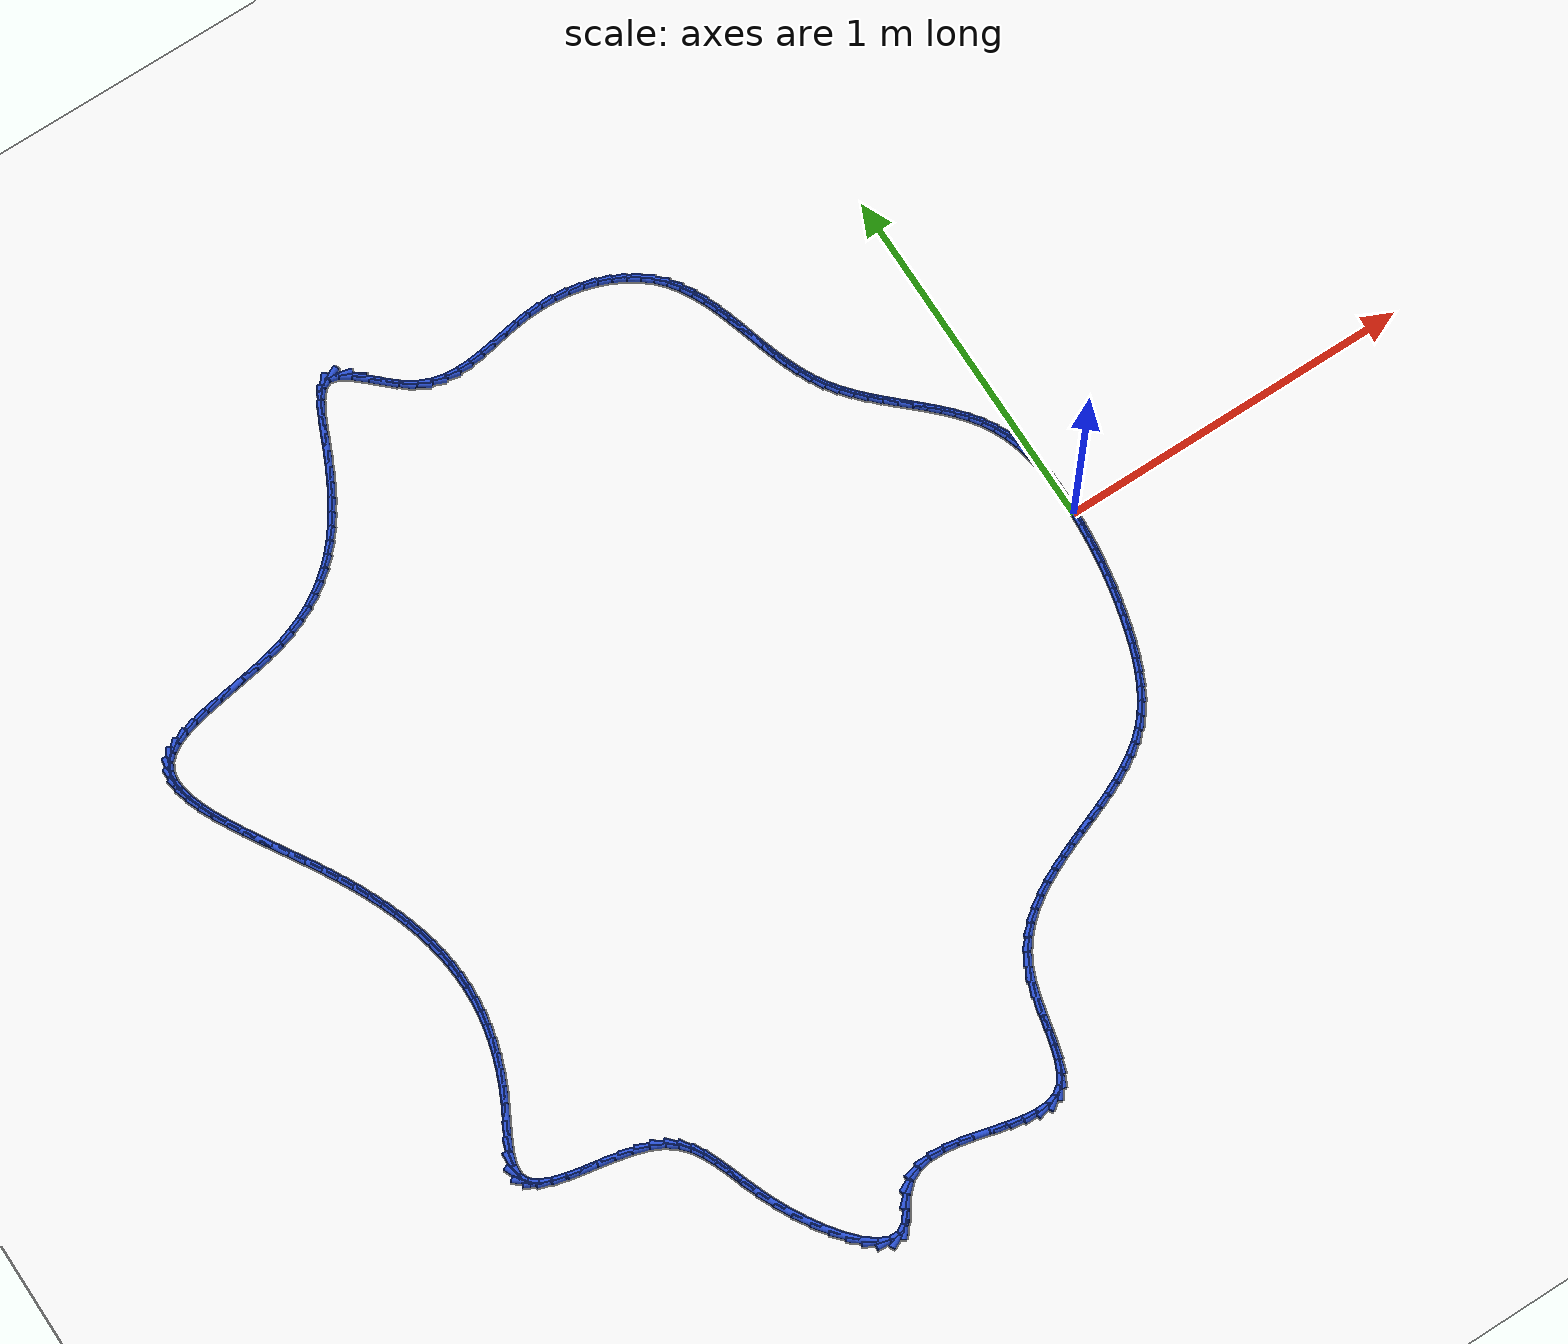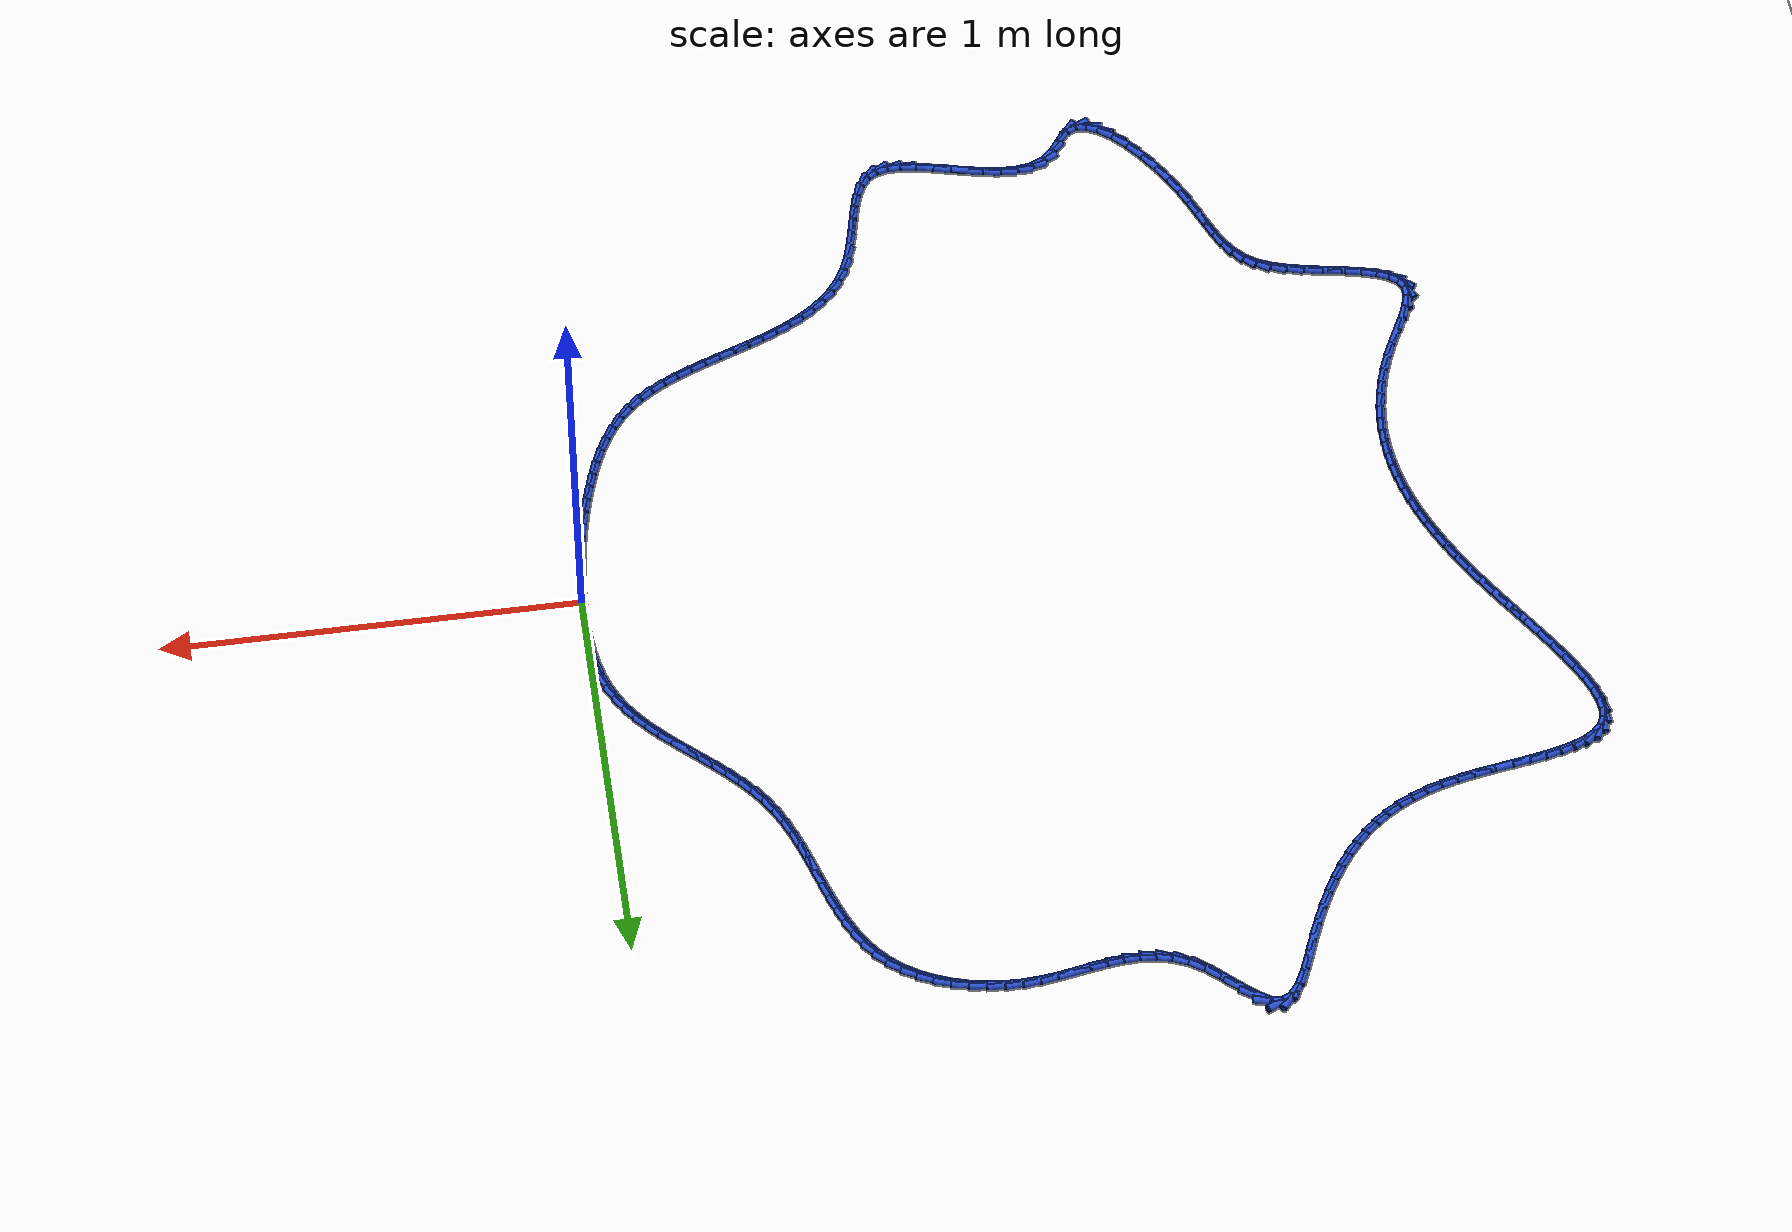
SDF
<sdf version="1.6">
 <world name="default">
  <light name="sun" type="directional">
   <pose>0 0 10 0 -0 0</pose>
   <diffuse>0.8 0.8 0.8 1</diffuse>
   <specular>0.2 0.2 0.2 1</specular>
   <attenuation>
    <range>1000</range>
    <constant>0.9</constant>
    <linear>0.01</linear>
    <quadratic>0.001</quadratic>
   </attenuation>
   <direction>-0.5 0.1 -0.9</direction>
  </light>
  <model name="ground_plane">
   <static>1</static>
   <link name="link">
    <collision name="collision">
     <geometry><plane><normal>0 0 1</normal><size>100 100</size></plane></geometry>
     <surface><friction><ode><mu>100</mu><mu2>50</mu2></ode></friction></surface>
    </collision>
    <visual name="visual">
     <cast_shadows>0</cast_shadows>
     <geometry><plane><normal>0 0 1</normal><size>100 100</size></plane></geometry>
     <material>
      <script><uri>file://media/materials/scripts/gazebo.material</uri><name>Gazebo/WhiteGlow</name></script>
     </material>
    </visual>
   </link>
  </model>
  <gravity>0 0 -9.8</gravity>
  <magnetic_field>6e-06 2.3e-05 -4.2e-05</magnetic_field>
  <atmosphere type="adiabatic"/>
  <physics name="default_physics" default="0" type="ode">
   <max_step_size>0.001</max_step_size>
   <real_time_factor>1</real_time_factor>
   <real_time_update_rate>1000</real_time_update_rate>
  </physics>
  <scene><ambient>0.4 0.4 0.4 1</ambient><background>0.7 0.7 0.7 1</background><shadows>1</shadows></scene>
  <spherical_coordinates>
   <surface_model>EARTH_WGS84</surface_model>
   <latitude_deg>0</latitude_deg>
   <longitude_deg>0</longitude_deg>
   <elevation>0</elevation>
   <heading_deg>0</heading_deg>
  </spherical_coordinates>
  <model name="line">
   <link name="link_0">
    <pose>-2.1033522146218786e-17 -1.3877787807814457e-17 0.01 0 1.57 1.5426861105589769</pose>
    <collision name="collision">
     <geometry><cylinder><radius>0.01</radius><length>0.08</length></cylinder></geometry>
    </collision>
    <visual name="visual">
     <material>
      <script><name>Gazebo/Blue</name><uri>file://media/materials/scripts/gazebo.material</uri></script>
     </material>
     <geometry><cylinder><radius>0.01</radius><length>0.08</length></cylinder></geometry>
    </visual>
   </link>
   <link name="link_1">
    <pose>0.0010906914985311805 0.0387903170800203 0.01 0 1.57 -1.5649687846395208</pose>
    <collision name="collision">
     <geometry><cylinder><radius>0.01</radius><length>0.08</length></cylinder></geometry>
    </collision>
    <visual name="visual">
     <material>
      <script><name>Gazebo/Blue</name><uri>file://media/materials/scripts/gazebo.material</uri></script>
     </material>
     <geometry><cylinder><radius>0.01</radius><length>0.08</length></cylinder></geometry>
    </visual>
   </link>
   <link name="link_2">
    <pose>0.0008631996236783038 0.07782723754406148 0.01 0 1.57 -1.5228137744650385</pose>
    <collision name="collision">
     <geometry><cylinder><radius>0.01</radius><length>0.08</length></cylinder></geometry>
    </collision>
    <visual name="visual">
     <material>
      <script><name>Gazebo/Blue</name><uri>file://media/materials/scripts/gazebo.material</uri></script>
     </material>
     <geometry><cylinder><radius>0.01</radius><length>0.08</length></cylinder></geometry>
    </visual>
   </link>
   <link name="link_3">
    <pose>-0.0010072002278098784 0.11677815026931554 0.01 0 1.57 -1.4715181799131993</pose>
    <collision name="collision">
     <geometry><cylinder><radius>0.01</radius><length>0.08</length></cylinder></geometry>
    </collision>
    <visual name="visual">
     <material>
      <script><name>Gazebo/Blue</name><uri>file://media/materials/scripts/gazebo.material</uri></script>
     </material>
     <geometry><cylinder><radius>0.01</radius><length>0.08</length></cylinder></geometry>
    </visual>
   </link>
   <link name="link_4">
    <pose>-0.004845232659184596 0.15531044413297435 0.01 0 1.57 -1.4099373749600639</pose>
    <collision name="collision">
     <geometry><cylinder><radius>0.01</radius><length>0.08</length></cylinder></geometry>
    </collision>
    <visual name="visual">
     <material>
      <script><name>Gazebo/Blue</name><uri>file://media/materials/scripts/gazebo.material</uri></script>
     </material>
     <geometry><cylinder><radius>0.01</radius><length>0.08</length></cylinder></geometry>
    </visual>
   </link>
   <link name="link_5">
    <pose>-0.01097562227369708 0.19309150801223007 0.01 0 1.57 -1.3367943161368112</pose>
    <collision name="collision">
     <geometry><cylinder><radius>0.01</radius><length>0.08</length></cylinder></geometry>
    </collision>
    <visual name="visual">
     <material>
      <script><name>Gazebo/Blue</name><uri>file://media/materials/scripts/gazebo.material</uri></script>
     </material>
     <geometry><cylinder><radius>0.01</radius><length>0.08</length></cylinder></geometry>
    </visual>
   </link>
   <link name="link_6">
    <pose>-0.019723093674598548 0.22978873078427461 0.01 0 1.57 -1.2508575145730594</pose>
    <collision name="collision">
     <geometry><cylinder><radius>0.01</radius><length>0.08</length></cylinder></geometry>
    </collision>
    <visual name="visual">
     <material>
      <script><name>Gazebo/Blue</name><uri>file://media/materials/scripts/gazebo.material</uri></script>
     </material>
     <geometry><cylinder><radius>0.01</radius><length>0.08</length></cylinder></geometry>
    </visual>
   </link>
   <link name="link_7">
    <pose>-0.031412371465140254 0.2650695013263001 0.01 0 1.57 -1.1512648486886758</pose>
    <collision name="collision">
     <geometry><cylinder><radius>0.01</radius><length>0.08</length></cylinder></geometry>
    </collision>
    <visual name="visual">
     <material>
      <script><name>Gazebo/Blue</name><uri>file://media/materials/scripts/gazebo.material</uri></script>
     </material>
     <geometry><cylinder><radius>0.01</radius><length>0.08</length></cylinder></geometry>
    </visual>
   </link>
   <link name="link_8">
    <pose>-0.04636795111524933 0.29860138621147914 0.01 0 1.57 -1.044689336991002</pose>
    <collision name="collision">
     <geometry><cylinder><radius>0.01</radius><length>0.08</length></cylinder></geometry>
    </collision>
    <visual name="visual">
     <material>
      <script><name>Gazebo/Blue</name><uri>file://media/materials/scripts/gazebo.material</uri></script>
     </material>
     <geometry><cylinder><radius>0.01</radius><length>0.08</length></cylinder></geometry>
    </visual>
   </link>
   <link name="link_9">
    <pose>-0.06471916566687594 0.3302033031060519 0.01 0 1.57 -0.9515311333777676</pose>
    <collision name="collision">
     <geometry><cylinder><radius>0.01</radius><length>0.08</length></cylinder></geometry>
    </collision>
    <visual name="visual">
     <material>
      <script><name>Gazebo/Blue</name><uri>file://media/materials/scripts/gazebo.material</uri></script>
     </material>
     <geometry><cylinder><radius>0.01</radius><length>0.08</length></cylinder></geometry>
    </visual>
   </link>
   <link name="link_10">
    <pose>-0.086044670504212 0.36012122762124 0.01 0 1.57 -0.8763383493266814</pose>
    <collision name="collision">
     <geometry><cylinder><radius>0.01</radius><length>0.08</length></cylinder></geometry>
    </collision>
    <visual name="visual">
     <material>
      <script><name>Gazebo/Blue</name><uri>file://media/materials/scripts/gazebo.material</uri></script>
     </material>
     <geometry><cylinder><radius>0.01</radius><length>0.08</length></cylinder></geometry>
    </visual>
   </link>
   <link name="link_11">
    <pose>-0.10982668859197266 0.3886759200091722 0.01 0 1.57 -0.8190387850133729</pose>
    <collision name="collision">
     <geometry><cylinder><radius>0.01</radius><length>0.08</length></cylinder></geometry>
    </collision>
    <visual name="visual">
     <material>
      <script><name>Gazebo/Blue</name><uri>file://media/materials/scripts/gazebo.material</uri></script>
     </material>
     <geometry><cylinder><radius>0.01</radius><length>0.08</length></cylinder></geometry>
    </visual>
   </link>
   <link name="link_12">
    <pose>-0.135547442894873 0.41618814052197733 0.01 0 1.57 -0.7788862932524584</pose>
    <collision name="collision">
     <geometry><cylinder><radius>0.01</radius><length>0.08</length></cylinder></geometry>
    </collision>
    <visual name="visual">
     <material>
      <script><name>Gazebo/Blue</name><uri>file://media/materials/scripts/gazebo.material</uri></script>
     </material>
     <geometry><cylinder><radius>0.01</radius><length>0.08</length></cylinder></geometry>
    </visual>
   </link>
   <link name="link_13">
    <pose>-0.1626891563776283 0.4429786494117849 0.01 0 1.57 -0.7549977820929026</pose>
    <collision name="collision">
     <geometry><cylinder><radius>0.01</radius><length>0.08</length></cylinder></geometry>
    </collision>
    <visual name="visual">
     <material>
      <script><name>Gazebo/Blue</name><uri>file://media/materials/scripts/gazebo.material</uri></script>
     </material>
     <geometry><cylinder><radius>0.01</radius><length>0.08</length></cylinder></geometry>
    </visual>
   </link>
   <link name="link_14">
    <pose>-0.19073405200495386 0.46936820693072373 0.01 0 1.57 -0.7466716957659749</pose>
    <collision name="collision">
     <geometry><cylinder><radius>0.01</radius><length>0.08</length></cylinder></geometry>
    </collision>
    <visual name="visual">
     <material>
      <script><name>Gazebo/Blue</name><uri>file://media/materials/scripts/gazebo.material</uri></script>
     </material>
     <geometry><cylinder><radius>0.01</radius><length>0.08</length></cylinder></geometry>
    </visual>
   </link>
   <link name="link_15">
    <pose>-0.21916435274156465 0.4956775733309226 0.01 0 1.57 -0.753539095530679</pose>
    <collision name="collision">
     <geometry><cylinder><radius>0.01</radius><length>0.08</length></cylinder></geometry>
    </collision>
    <visual name="visual">
     <material>
      <script><name>Gazebo/Blue</name><uri>file://media/materials/scripts/gazebo.material</uri></script>
     </material>
     <geometry><cylinder><radius>0.01</radius><length>0.08</length></cylinder></geometry>
    </visual>
   </link>
   <link name="link_16">
    <pose>-0.24746228155217595 0.5222275088645107 0.01 0 1.57 -0.7756007360360908</pose>
    <collision name="collision">
     <geometry><cylinder><radius>0.01</radius><length>0.08</length></cylinder></geometry>
    </collision>
    <visual name="visual">
     <material>
      <script><name>Gazebo/Blue</name><uri>file://media/materials/scripts/gazebo.material</uri></script>
     </material>
     <geometry><cylinder><radius>0.01</radius><length>0.08</length></cylinder></geometry>
    </visual>
   </link>
   <link name="link_17">
    <pose>-0.27511006140150296 0.5493387737836171 0.01 0 1.57 -0.8131753307497481</pose>
    <collision name="collision">
     <geometry><cylinder><radius>0.01</radius><length>0.08</length></cylinder></geometry>
    </collision>
    <visual name="visual">
     <material>
      <script><name>Gazebo/Blue</name><uri>file://media/materials/scripts/gazebo.material</uri></script>
     </material>
     <geometry><cylinder><radius>0.01</radius><length>0.08</length></cylinder></geometry>
    </visual>
   </link>
   <link name="link_18">
    <pose>-0.30158991525426093 0.5773321283403706 0.01 0 1.57 -0.8667522805038841</pose>
    <collision name="collision">
     <geometry><cylinder><radius>0.01</radius><length>0.08</length></cylinder></geometry>
    </collision>
    <visual name="visual">
     <material>
      <script><name>Gazebo/Blue</name><uri>file://media/materials/scripts/gazebo.material</uri></script>
     </material>
     <geometry><cylinder><radius>0.01</radius><length>0.08</length></cylinder></geometry>
    </visual>
   </link>
   <link name="link_19">
    <pose>-0.32638406607516496 0.6065283327869004 0.01 0 1.57 -0.9367192703689053</pose>
    <collision name="collision">
     <geometry><cylinder><radius>0.01</radius><length>0.08</length></cylinder></geometry>
    </collision>
    <visual name="visual">
     <material>
      <script><name>Gazebo/Blue</name><uri>file://media/materials/scripts/gazebo.material</uri></script>
     </material>
     <geometry><cylinder><radius>0.01</radius><length>0.08</length></cylinder></geometry>
    </visual>
   </link>
   <link name="link_20">
    <pose>-0.3489747368289302 0.6372481473753355 0.01 0 1.57 -1.0219617712954638</pose>
    <collision name="collision">
     <geometry><cylinder><radius>0.01</radius><length>0.08</length></cylinder></geometry>
    </collision>
    <visual name="visual">
     <material>
      <script><name>Gazebo/Blue</name><uri>file://media/materials/scripts/gazebo.material</uri></script>
     </material>
     <geometry><cylinder><radius>0.01</radius><length>0.08</length></cylinder></geometry>
    </visual>
   </link>
   <link name="link_21">
    <pose>-0.3688749897850871 0.6697913379379333 0.01 0 1.57 -1.104842922229998</pose>
    <collision name="collision">
     <geometry><cylinder><radius>0.01</radius><length>0.08</length></cylinder></geometry>
    </collision>
    <visual name="visual">
     <material>
      <script><name>Gazebo/Blue</name><uri>file://media/materials/scripts/gazebo.material</uri></script>
     </material>
     <geometry><cylinder><radius>0.01</radius><length>0.08</length></cylinder></geometry>
    </visual>
   </link>
   <link name="link_22">
    <pose>-0.3861270352582304 0.7040974431131511 0.01 0 1.57 -1.1709160763228699</pose>
    <collision name="collision">
     <geometry><cylinder><radius>0.01</radius><length>0.08</length></cylinder></geometry>
    </collision>
    <visual name="visual">
     <material>
      <script><name>Gazebo/Blue</name><uri>file://media/materials/scripts/gazebo.material</uri></script>
     </material>
     <geometry><cylinder><radius>0.01</radius><length>0.08</length></cylinder></geometry>
    </visual>
   </link>
   <link name="link_23">
    <pose>-0.40121808702933937 0.7398030573040436 0.01 0 1.57 -1.2202488985502462</pose>
    <collision name="collision">
     <geometry><cylinder><radius>0.01</radius><length>0.08</length></cylinder></geometry>
    </collision>
    <visual name="visual">
     <material>
      <script><name>Gazebo/Blue</name><uri>file://media/materials/scripts/gazebo.material</uri></script>
     </material>
     <geometry><cylinder><radius>0.01</radius><length>0.08</length></cylinder></geometry>
    </visual>
   </link>
   <link name="link_24">
    <pose>-0.41464921088020584 0.776535344911178 0.01 0 1.57 -1.253621303977735</pose>
    <collision name="collision">
     <geometry><cylinder><radius>0.01</radius><length>0.08</length></cylinder></geometry>
    </collision>
    <visual name="visual">
     <material>
      <script><name>Gazebo/Blue</name><uri>file://media/materials/scripts/gazebo.material</uri></script>
     </material>
     <geometry><cylinder><radius>0.01</radius><length>0.08</length></cylinder></geometry>
    </visual>
   </link>
   <link name="link_25">
    <pose>-0.4269214725926214 0.8139214703351213 0.01 0 1.57 -1.271701385451119</pose>
    <collision name="collision">
     <geometry><cylinder><radius>0.01</radius><length>0.08</length></cylinder></geometry>
    </collision>
    <visual name="visual">
     <material>
      <script><name>Gazebo/Blue</name><uri>file://media/materials/scripts/gazebo.material</uri></script>
     </material>
     <geometry><cylinder><radius>0.01</radius><length>0.08</length></cylinder></geometry>
    </visual>
   </link>
   <link name="link_26">
    <pose>-0.438535937948378 0.8515885979764412 0.01 0 1.57 -1.2748251835789532</pose>
    <collision name="collision">
     <geometry><cylinder><radius>0.01</radius><length>0.08</length></cylinder></geometry>
    </collision>
    <visual name="visual">
     <material>
      <script><name>Gazebo/Blue</name><uri>file://media/materials/scripts/gazebo.material</uri></script>
     </material>
     <geometry><cylinder><radius>0.01</radius><length>0.08</length></cylinder></geometry>
    </visual>
   </link>
   <link name="link_27">
    <pose>-0.4499936727292669 0.8891638922357038 0.01 0 1.57 -1.26288684977311</pose>
    <collision name="collision">
     <geometry><cylinder><radius>0.01</radius><length>0.08</length></cylinder></geometry>
    </collision>
    <visual name="visual">
     <material>
      <script><name>Gazebo/Blue</name><uri>file://media/materials/scripts/gazebo.material</uri></script>
     </material>
     <geometry><cylinder><radius>0.01</radius><length>0.08</length></cylinder></geometry>
    </visual>
   </link>
   <link name="link_28">
    <pose>-0.46179574271708024 0.9262745175134771 0.01 0 1.57 -1.235303855261491</pose>
    <collision name="collision">
     <geometry><cylinder><radius>0.01</radius><length>0.08</length></cylinder></geometry>
    </collision>
    <visual name="visual">
     <material>
      <script><name>Gazebo/Blue</name><uri>file://media/materials/scripts/gazebo.material</uri></script>
     </material>
     <geometry><cylinder><radius>0.01</radius><length>0.08</length></cylinder></geometry>
    </visual>
   </link>
   <link name="link_29">
    <pose>-0.4744432136936095 0.9625476382103278 0.01 0 1.57 -1.1910566535881146</pose>
    <collision name="collision">
     <geometry><cylinder><radius>0.01</radius><length>0.08</length></cylinder></geometry>
    </collision>
    <visual name="visual">
     <material>
      <script><name>Gazebo/Blue</name><uri>file://media/materials/scripts/gazebo.material</uri></script>
     </material>
     <geometry><cylinder><radius>0.01</radius><length>0.08</length></cylinder></geometry>
    </visual>
   </link>
   <link name="link_30">
    <pose>-0.4884371514406466 0.9976104187268234 0.01 0 1.57 -1.128843977385254</pose>
    <collision name="collision">
     <geometry><cylinder><radius>0.01</radius><length>0.08</length></cylinder></geometry>
    </collision>
    <visual name="visual">
     <material>
      <script><name>Gazebo/Blue</name><uri>file://media/materials/scripts/gazebo.material</uri></script>
     </material>
     <geometry><cylinder><radius>0.01</radius><length>0.08</length></cylinder></geometry>
    </visual>
   </link>
   <link name="link_31">
    <pose>-0.5042786217399833 1.0310900234635312 0.01 0 1.57 -1.047437558927517</pose>
    <collision name="collision">
     <geometry><cylinder><radius>0.01</radius><length>0.08</length></cylinder></geometry>
    </collision>
    <visual name="visual">
     <material>
      <script><name>Gazebo/Blue</name><uri>file://media/materials/scripts/gazebo.material</uri></script>
     </material>
     <geometry><cylinder><radius>0.01</radius><length>0.08</length></cylinder></geometry>
    </visual>
   </link>
   <link name="link_32">
    <pose>-0.5224686903734108 1.0626136168210176 0.01 0 1.57 -0.9463331773087679</pose>
    <collision name="collision">
     <geometry><cylinder><radius>0.01</radius><length>0.08</length></cylinder></geometry>
    </collision>
    <visual name="visual">
     <material>
      <script><name>Gazebo/Blue</name><uri>file://media/materials/scripts/gazebo.material</uri></script>
     </material>
     <geometry><cylinder><radius>0.01</radius><length>0.08</length></cylinder></geometry>
    </visual>
   </link>
   <link name="link_33">
    <pose>-0.5435084231227215 1.0918083631998508 0.01 0 1.57 -0.8267347233099263</pose>
    <collision name="collision">
     <geometry><cylinder><radius>0.01</radius><length>0.08</length></cylinder></geometry>
    </collision>
    <visual name="visual">
     <material>
      <script><name>Gazebo/Blue</name><uri>file://media/materials/scripts/gazebo.material</uri></script>
     </material>
     <geometry><cylinder><radius>0.01</radius><length>0.08</length></cylinder></geometry>
    </visual>
   </link>
   <link name="link_34">
    <pose>-0.5678974631067041 1.1183019132170997 0.01 0 1.57 -0.6992649917668289</pose>
    <collision name="collision">
     <geometry><cylinder><radius>0.01</radius><length>0.08</length></cylinder></geometry>
    </collision>
    <visual name="visual">
     <material>
      <script><name>Gazebo/Blue</name><uri>file://media/materials/scripts/gazebo.material</uri></script>
     </material>
     <geometry><cylinder><radius>0.01</radius><length>0.08</length></cylinder></geometry>
    </visual>
   </link>
   <link name="link_35">
    <pose>-0.5958572411078632 1.1418170007449144 0.01 0 1.57 -0.5814417226303559</pose>
    <collision name="collision">
     <geometry><cylinder><radius>0.01</radius><length>0.08</length></cylinder></geometry>
    </collision>
    <visual name="visual">
     <material>
      <script><name>Gazebo/Blue</name><uri>file://media/materials/scripts/gazebo.material</uri></script>
     </material>
     <geometry><cylinder><radius>0.01</radius><length>0.08</length></cylinder></geometry>
    </visual>
   </link>
   <link name="link_36">
    <pose>-0.6269995718535288 1.1622847051215315 0.01 0 1.57 -0.47424900157333966</pose>
    <collision name="collision">
     <geometry><cylinder><radius>0.01</radius><length>0.08</length></cylinder></geometry>
    </collision>
    <visual name="visual">
     <material>
      <script><name>Gazebo/Blue</name><uri>file://media/materials/scripts/gazebo.material</uri></script>
     </material>
     <geometry><cylinder><radius>0.01</radius><length>0.08</length></cylinder></geometry>
    </visual>
   </link>
   <link name="link_37">
    <pose>-0.6608554802105862 1.1796637168364834 0.01 0 1.57 -0.3759323834869725</pose>
    <collision name="collision">
     <geometry><cylinder><radius>0.01</radius><length>0.08</length></cylinder></geometry>
    </collision>
    <visual name="visual">
     <material>
      <script><name>Gazebo/Blue</name><uri>file://media/materials/scripts/gazebo.material</uri></script>
     </material>
     <geometry><cylinder><radius>0.01</radius><length>0.08</length></cylinder></geometry>
    </visual>
   </link>
   <link name="link_38">
    <pose>-0.6969559910459185 1.1939127263792981 0.01 0 1.57 -0.28453585115900837</pose>
    <collision name="collision">
     <geometry><cylinder><radius>0.01</radius><length>0.08</length></cylinder></geometry>
    </collision>
    <visual name="visual">
     <material>
      <script><name>Gazebo/Blue</name><uri>file://media/materials/scripts/gazebo.material</uri></script>
     </material>
     <geometry><cylinder><radius>0.01</radius><length>0.08</length></cylinder></geometry>
    </visual>
   </link>
   <link name="link_39">
    <pose>-0.7348321292264106 1.2049904242395075 0.01 0 1.57 -0.19809530270771414</pose>
    <collision name="collision">
     <geometry><cylinder><radius>0.01</radius><length>0.08</length></cylinder></geometry>
    </collision>
    <visual name="visual">
     <material>
      <script><name>Gazebo/Blue</name><uri>file://media/materials/scripts/gazebo.material</uri></script>
     </material>
     <geometry><cylinder><radius>0.01</radius><length>0.08</length></cylinder></geometry>
    </visual>
   </link>
   <link name="link_40">
    <pose>-0.7740149196189464 1.2128555009066413 0.01 0 1.57 -0.11471384654005204</pose>
    <collision name="collision">
     <geometry><cylinder><radius>0.01</radius><length>0.08</length></cylinder></geometry>
    </collision>
    <visual name="visual">
     <material>
      <script><name>Gazebo/Blue</name><uri>file://media/materials/scripts/gazebo.material</uri></script>
     </material>
     <geometry><cylinder><radius>0.01</radius><length>0.08</length></cylinder></geometry>
    </visual>
   </link>
   <link name="link_41">
    <pose>-0.8140353870904102 1.2174666468702302 0.01 0 1.57 -0.03256913805982124</pose>
    <collision name="collision">
     <geometry><cylinder><radius>0.01</radius><length>0.08</length></cylinder></geometry>
    </collision>
    <visual name="visual">
     <material>
      <script><name>Gazebo/Blue</name><uri>file://media/materials/scripts/gazebo.material</uri></script>
     </material>
     <geometry><cylinder><radius>0.01</radius><length>0.08</length></cylinder></geometry>
    </visual>
   </link>
   <link name="link_42">
    <pose>-0.8544245565076862 1.2187825526198042 0.01 0 1.57 0.04973553143149947</pose>
    <collision name="collision">
     <geometry><cylinder><radius>0.01</radius><length>0.08</length></cylinder></geometry>
    </collision>
    <visual name="visual">
     <material>
      <script><name>Gazebo/Blue</name><uri>file://media/materials/scripts/gazebo.material</uri></script>
     </material>
     <geometry><cylinder><radius>0.01</radius><length>0.08</length></cylinder></geometry>
    </visual>
   </link>
   <link name="link_43">
    <pose>-0.894718693326517 1.2167768482532169 0.01 0 1.57 0.12036940523979064</pose>
    <collision name="collision">
     <geometry><cylinder><radius>0.01</radius><length>0.08</length></cylinder></geometry>
    </collision>
    <visual name="visual">
     <material>
      <script><name>Gazebo/Blue</name><uri>file://media/materials/scripts/gazebo.material</uri></script>
     </material>
     <geometry><cylinder><radius>0.01</radius><length>0.08</length></cylinder></geometry>
    </visual>
   </link>
   <link name="link_44">
    <pose>-0.9346383099198979 1.211948405754866 0.01 0 1.57 0.16313081692728298</pose>
    <collision name="collision">
     <geometry><cylinder><radius>0.01</radius><length>0.08</length></cylinder></geometry>
    </collision>
    <visual name="visual">
     <material>
      <script><name>Gazebo/Blue</name><uri>file://media/materials/scripts/gazebo.material</uri></script>
     </material>
     <geometry><cylinder><radius>0.01</radius><length>0.08</length></cylinder></geometry>
    </visual>
   </link>
   <link name="link_45">
    <pose>-0.9741325648188227 1.2054479101281605 0.01 0 1.57 0.1769865569835285</pose>
    <collision name="collision">
     <geometry><cylinder><radius>0.01</radius><length>0.08</length></cylinder></geometry>
    </collision>
    <visual name="visual">
     <material>
      <script><name>Gazebo/Blue</name><uri>file://media/materials/scripts/gazebo.material</uri></script>
     </material>
     <geometry><cylinder><radius>0.01</radius><length>0.08</length></cylinder></geometry>
    </visual>
   </link>
   <link name="link_46">
    <pose>-1.0131648669443891 1.1984666706751064 0.01 0 1.57 0.16131788779947123</pose>
    <collision name="collision">
     <geometry><cylinder><radius>0.01</radius><length>0.08</length></cylinder></geometry>
    </collision>
    <visual name="visual">
     <material>
      <script><name>Gazebo/Blue</name><uri>file://media/materials/scripts/gazebo.material</uri></script>
     </material>
     <geometry><cylinder><radius>0.01</radius><length>0.08</length></cylinder></geometry>
    </visual>
   </link>
   <link name="link_47">
    <pose>-1.051698625217694 1.1921959966977087 0.01 0 1.57 0.11446994997318768</pose>
    <collision name="collision">
     <geometry><cylinder><radius>0.01</radius><length>0.08</length></cylinder></geometry>
    </collision>
    <visual name="visual">
     <material>
      <script><name>Gazebo/Blue</name><uri>file://media/materials/scripts/gazebo.material</uri></script>
     </material>
     <geometry><cylinder><radius>0.01</radius><length>0.08</length></cylinder></geometry>
    </visual>
   </link>
   <link name="link_48">
    <pose>-1.0896972485598355 1.187827197497973 0.01 0 1.57 0.03406965630708238</pose>
    <collision name="collision">
     <geometry><cylinder><radius>0.01</radius><length>0.08</length></cylinder></geometry>
    </collision>
    <visual name="visual">
     <material>
      <script><name>Gazebo/Blue</name><uri>file://media/materials/scripts/gazebo.material</uri></script>
     </material>
     <geometry><cylinder><radius>0.01</radius><length>0.08</length></cylinder></geometry>
    </visual>
   </link>
   <link name="link_49">
    <pose>-1.12712414589191 1.1865515823779043 0.01 0 1.57 -0.08154053600788012</pose>
    <collision name="collision">
     <geometry><cylinder><radius>0.01</radius><length>0.08</length></cylinder></geometry>
    </collision>
    <visual name="visual">
     <material>
      <script><name>Gazebo/Blue</name><uri>file://media/materials/scripts/gazebo.material</uri></script>
     </material>
     <geometry><cylinder><radius>0.01</radius><length>0.08</length></cylinder></geometry>
    </visual>
   </link>
   <link name="link_50">
    <pose>-1.1639427261350153 1.1895604606395085 0.01 0 1.57 -0.23038929816476642</pose>
    <collision name="collision">
     <geometry><cylinder><radius>0.01</radius><length>0.08</length></cylinder></geometry>
    </collision>
    <visual name="visual">
     <material>
      <script><name>Gazebo/Blue</name><uri>file://media/materials/scripts/gazebo.material</uri></script>
     </material>
     <geometry><cylinder><radius>0.01</radius><length>0.08</length></cylinder></geometry>
    </visual>
   </link>
   <link name="link_51">
    <pose>-1.2001163982102483 1.1980451415847897 0.01 0 1.57 -0.40348325662939266</pose>
    <collision name="collision">
     <geometry><cylinder><radius>0.01</radius><length>0.08</length></cylinder></geometry>
    </collision>
    <visual name="visual">
     <material>
      <script><name>Gazebo/Blue</name><uri>file://media/materials/scripts/gazebo.material</uri></script>
     </material>
     <geometry><cylinder><radius>0.01</radius><length>0.08</length></cylinder></geometry>
    </visual>
   </link>
   <link name="link_52">
    <pose>-1.2356085710387072 1.2131969345157547 0.01 0 1.57 -0.5828335361775304</pose>
    <collision name="collision">
     <geometry><cylinder><radius>0.01</radius><length>0.08</length></cylinder></geometry>
    </collision>
    <visual name="visual">
     <material>
      <script><name>Gazebo/Blue</name><uri>file://media/materials/scripts/gazebo.material</uri></script>
     </material>
     <geometry><cylinder><radius>0.01</radius><length>0.08</length></cylinder></geometry>
    </visual>
   </link>
   <link name="link_53">
    <pose>-1.2703774977852433 1.2361175084572775 0.01 0 1.57 -0.7101146643983015</pose>
    <collision name="collision">
     <geometry><cylinder><radius>0.01</radius><length>0.08</length></cylinder></geometry>
    </collision>
    <visual name="visual">
     <material>
      <script><name>Gazebo/Blue</name><uri>file://media/materials/scripts/gazebo.material</uri></script>
     </material>
     <geometry><cylinder><radius>0.01</radius><length>0.08</length></cylinder></geometry>
    </visual>
   </link>
   <link name="link_54">
    <pose>-1.304226719235444 1.2652186340190867 0.01 0 1.57 -0.7544499469010513</pose>
    <collision name="collision">
     <geometry><cylinder><radius>0.01</radius><length>0.08</length></cylinder></geometry>
    </collision>
    <visual name="visual">
     <material>
      <script><name>Gazebo/Blue</name><uri>file://media/materials/scripts/gazebo.material</uri></script>
     </material>
     <geometry><cylinder><radius>0.01</radius><length>0.08</length></cylinder></geometry>
    </visual>
   </link>
   <link name="link_55">
    <pose>-1.3367818515105183 1.295818604255986 0.01 0 1.57 -0.7230156452354544</pose>
    <collision name="collision">
     <geometry><cylinder><radius>0.01</radius><length>0.08</length></cylinder></geometry>
    </collision>
    <visual name="visual">
     <material>
      <script><name>Gazebo/Blue</name><uri>file://media/materials/scripts/gazebo.material</uri></script>
     </material>
     <geometry><cylinder><radius>0.01</radius><length>0.08</length></cylinder></geometry>
    </visual>
   </link>
   <link name="link_56">
    <pose>-1.3676586840603184 1.3230648613326654 0.01 0 1.57 -0.5839175451651349</pose>
    <collision name="collision">
     <geometry><cylinder><radius>0.01</radius><length>0.08</length></cylinder></geometry>
    </collision>
    <visual name="visual">
     <material>
      <script><name>Gazebo/Blue</name><uri>file://media/materials/scripts/gazebo.material</uri></script>
     </material>
     <geometry><cylinder><radius>0.01</radius><length>0.08</length></cylinder></geometry>
    </visual>
   </link>
   <link name="link_57">
    <pose>-1.3964730063346962 1.342104847413813 0.01 0 1.57 -0.22306258374148705</pose>
    <collision name="collision">
     <geometry><cylinder><radius>0.01</radius><length>0.08</length></cylinder></geometry>
    </collision>
    <visual name="visual">
     <material>
      <script><name>Gazebo/Blue</name><uri>file://media/materials/scripts/gazebo.material</uri></script>
     </material>
     <geometry><cylinder><radius>0.01</radius><length>0.08</length></cylinder></geometry>
    </visual>
   </link>
   <link name="link_58">
    <pose>-1.4228406077835043 1.3480860046641199 0.01 0 1.57 0.430712198860181</pose>
    <collision name="collision">
     <geometry><cylinder><radius>0.01</radius><length>0.08</length></cylinder></geometry>
    </collision>
    <visual name="visual">
     <material>
      <script><name>Gazebo/Blue</name><uri>file://media/materials/scripts/gazebo.material</uri></script>
     </material>
     <geometry><cylinder><radius>0.01</radius><length>0.08</length></cylinder></geometry>
    </visual>
   </link>
   <link name="link_59">
    <pose>-1.4464993081471151 1.337215226870837 0.01 0 1.57 0.8729669830696112</pose>
    <collision name="collision">
     <geometry><cylinder><radius>0.01</radius><length>0.08</length></cylinder></geometry>
    </collision>
    <visual name="visual">
     <material>
      <script><name>Gazebo/Blue</name><uri>file://media/materials/scripts/gazebo.material</uri></script>
     </material>
     <geometry><cylinder><radius>0.01</radius><length>0.08</length></cylinder></geometry>
    </visual>
   </link>
   <link name="link_60">
    <pose>-1.4678802511396374 1.3117187592937494 0.01 0 1.57 1.0657281998502035</pose>
    <collision name="collision">
     <geometry><cylinder><radius>0.01</radius><length>0.08</length></cylinder></geometry>
    </collision>
    <visual name="visual">
     <material>
      <script><name>Gazebo/Blue</name><uri>file://media/materials/scripts/gazebo.material</uri></script>
     </material>
     <geometry><cylinder><radius>0.01</radius><length>0.08</length></cylinder></geometry>
    </visual>
   </link>
   <link name="link_61">
    <pose>-1.4876591190119548 1.2759458999892876 0.01 0 1.57 1.146171779118305</pose>
    <collision name="collision">
     <geometry><cylinder><radius>0.01</radius><length>0.08</length></cylinder></geometry>
    </collision>
    <visual name="visual">
     <material>
      <script><name>Gazebo/Blue</name><uri>file://media/materials/scripts/gazebo.material</uri></script>
     </material>
     <geometry><cylinder><radius>0.01</radius><length>0.08</length></cylinder></geometry>
    </visual>
   </link>
   <link name="link_62">
    <pose>-1.5065118703647598 1.234248346248146 0.01 0 1.57 1.1647811419523861</pose>
    <collision name="collision">
     <geometry><cylinder><radius>0.01</radius><length>0.08</length></cylinder></geometry>
    </collision>
    <visual name="visual">
     <material>
      <script><name>Gazebo/Blue</name><uri>file://media/materials/scripts/gazebo.material</uri></script>
     </material>
     <geometry><cylinder><radius>0.01</radius><length>0.08</length></cylinder></geometry>
    </visual>
   </link>
   <link name="link_63">
    <pose>-1.525114354740891 1.1909768733549864 0.01 0 1.57 1.1430470830943131</pose>
    <collision name="collision">
     <geometry><cylinder><radius>0.01</radius><length>0.08</length></cylinder></geometry>
    </collision>
    <visual name="visual">
     <material>
      <script><name>Gazebo/Blue</name><uri>file://media/materials/scripts/gazebo.material</uri></script>
     </material>
     <geometry><cylinder><radius>0.01</radius><length>0.08</length></cylinder></geometry>
    </visual>
   </link>
   <link name="link_64">
    <pose>-1.5440257036756722 1.149495489452441 0.01 0 1.57 1.1103010484580846</pose>
    <collision name="collision">
     <geometry><cylinder><radius>0.01</radius><length>0.08</length></cylinder></geometry>
    </collision>
    <visual name="visual">
     <material>
      <script><name>Gazebo/Blue</name><uri>file://media/materials/scripts/gazebo.material</uri></script>
     </material>
     <geometry><cylinder><radius>0.01</radius><length>0.08</length></cylinder></geometry>
    </visual>
   </link>
   <link name="link_65">
    <pose>-1.5634664538354153 1.110305625619717 0.01 0 1.57 1.0715488552188424</pose>
    <collision name="collision">
     <geometry><cylinder><radius>0.01</radius><length>0.08</length></cylinder></geometry>
    </collision>
    <visual name="visual">
     <material>
      <script><name>Gazebo/Blue</name><uri>file://media/materials/scripts/gazebo.material</uri></script>
     </material>
     <geometry><cylinder><radius>0.01</radius><length>0.08</length></cylinder></geometry>
    </visual>
   </link>
   <link name="link_66">
    <pose>-1.583596091474342 1.0733925754355589 0.01 0 1.57 1.0264087159504258</pose>
    <collision name="collision">
     <geometry><cylinder><radius>0.01</radius><length>0.08</length></cylinder></geometry>
    </collision>
    <visual name="visual">
     <material>
      <script><name>Gazebo/Blue</name><uri>file://media/materials/scripts/gazebo.material</uri></script>
     </material>
     <geometry><cylinder><radius>0.01</radius><length>0.08</length></cylinder></geometry>
    </visual>
   </link>
   <link name="link_67">
    <pose>-1.6045741028466738 1.0387416324787127 0.01 0 1.57 0.9746446581970213</pose>
    <collision name="collision">
     <geometry><cylinder><radius>0.01</radius><length>0.08</length></cylinder></geometry>
    </collision>
    <visual name="visual">
     <material>
      <script><name>Gazebo/Blue</name><uri>file://media/materials/scripts/gazebo.material</uri></script>
     </material>
     <geometry><cylinder><radius>0.01</radius><length>0.08</length></cylinder></geometry>
    </visual>
   </link>
   <link name="link_68">
    <pose>-1.6265599742066326 1.0063380903279235 0.01 0 1.57 0.9162496301693195</pose>
    <collision name="collision">
     <geometry><cylinder><radius>0.01</radius><length>0.08</length></cylinder></geometry>
    </collision>
    <visual name="visual">
     <material>
      <script><name>Gazebo/Blue</name><uri>file://media/materials/scripts/gazebo.material</uri></script>
     </material>
     <geometry><cylinder><radius>0.01</radius><length>0.08</length></cylinder></geometry>
    </visual>
   </link>
   <link name="link_69">
    <pose>-1.6497131918084393 0.9761672425619358 0.01 0 1.57 0.851534961629581</pose>
    <collision name="collision">
     <geometry><cylinder><radius>0.01</radius><length>0.08</length></cylinder></geometry>
    </collision>
    <visual name="visual">
     <material>
      <script><name>Gazebo/Blue</name><uri>file://media/materials/scripts/gazebo.material</uri></script>
     </material>
     <geometry><cylinder><radius>0.01</radius><length>0.08</length></cylinder></geometry>
    </visual>
   </link>
   <link name="link_70">
    <pose>-1.6741932419063168 0.9482143827594958 0.01 0 1.57 0.7812062394298878</pose>
    <collision name="collision">
     <geometry><cylinder><radius>0.01</radius><length>0.08</length></cylinder></geometry>
    </collision>
    <visual name="visual">
     <material>
      <script><name>Gazebo/Blue</name><uri>file://media/materials/scripts/gazebo.material</uri></script>
     </material>
     <geometry><cylinder><radius>0.01</radius><length>0.08</length></cylinder></geometry>
    </visual>
   </link>
   <link name="link_71">
    <pose>-1.7001596107544854 0.9224648044993482 0.01 0 1.57 0.7063970261942405</pose>
    <collision name="collision">
     <geometry><cylinder><radius>0.01</radius><length>0.08</length></cylinder></geometry>
    </collision>
    <visual name="visual">
     <material>
      <script><name>Gazebo/Blue</name><uri>file://media/materials/scripts/gazebo.material</uri></script>
     </material>
     <geometry><cylinder><radius>0.01</radius><length>0.08</length></cylinder></geometry>
    </visual>
   </link>
   <link name="link_72">
    <pose>-1.727771784607168 0.8989038013602382 0.01 0 1.57 0.6286320579274024</pose>
    <collision name="collision">
     <geometry><cylinder><radius>0.01</radius><length>0.08</length></cylinder></geometry>
    </collision>
    <visual name="visual">
     <material>
      <script><name>Gazebo/Blue</name><uri>file://media/materials/scripts/gazebo.material</uri></script>
     </material>
     <geometry><cylinder><radius>0.01</radius><length>0.08</length></cylinder></geometry>
    </visual>
   </link>
   <link name="link_73">
    <pose>-1.7571892497185857 0.8775166669209103 0.01 0 1.57 0.5497071091050244</pose>
    <collision name="collision">
     <geometry><cylinder><radius>0.01</radius><length>0.08</length></cylinder></geometry>
    </collision>
    <visual name="visual">
     <material>
      <script><name>Gazebo/Blue</name><uri>file://media/materials/scripts/gazebo.material</uri></script>
     </material>
     <geometry><cylinder><radius>0.01</radius><length>0.08</length></cylinder></geometry>
    </visual>
   </link>
   <link name="link_74">
    <pose>-1.7885714923429603 0.8582886947601113 0.01 0 1.57 0.47150182891055975</pose>
    <collision name="collision">
     <geometry><cylinder><radius>0.01</radius><length>0.08</length></cylinder></geometry>
    </collision>
    <visual name="visual">
     <material>
      <script><name>Gazebo/Blue</name><uri>file://media/materials/scripts/gazebo.material</uri></script>
     </material>
     <geometry><cylinder><radius>0.01</radius><length>0.08</length></cylinder></geometry>
    </visual>
   </link>
   <link name="link_75">
    <pose>-1.8220779987345135 0.841205178456585 0.01 0 1.57 0.39577063048852296</pose>
    <collision name="collision">
     <geometry><cylinder><radius>0.01</radius><length>0.08</length></cylinder></geometry>
    </collision>
    <visual name="visual">
     <material>
      <script><name>Gazebo/Blue</name><uri>file://media/materials/scripts/gazebo.material</uri></script>
     </material>
     <geometry><cylinder><radius>0.01</radius><length>0.08</length></cylinder></geometry>
    </visual>
   </link>
   <link name="link_76">
    <pose>-1.857868255147467 0.8262514115890771 0.01 0 1.57 0.3239669584710281</pose>
    <collision name="collision">
     <geometry><cylinder><radius>0.01</radius><length>0.08</length></cylinder></geometry>
    </collision>
    <visual name="visual">
     <material>
      <script><name>Gazebo/Blue</name><uri>file://media/materials/scripts/gazebo.material</uri></script>
     </material>
     <geometry><cylinder><radius>0.01</radius><length>0.08</length></cylinder></geometry>
    </visual>
   </link>
   <link name="link_77">
    <pose>-1.8961017478360418 0.8134126877363329 0.01 0 1.57 0.2581279239047877</pose>
    <collision name="collision">
     <geometry><cylinder><radius>0.01</radius><length>0.08</length></cylinder></geometry>
    </collision>
    <visual name="visual">
     <material>
      <script><name>Gazebo/Blue</name><uri>file://media/materials/scripts/gazebo.material</uri></script>
     </material>
     <geometry><cylinder><radius>0.01</radius><length>0.08</length></cylinder></geometry>
    </visual>
   </link>
   <link name="link_78">
    <pose>-1.9368803018167802 0.8026464163270444 0.01 0 1.57 0.20832052276798002</pose>
    <collision name="collision">
     <geometry><cylinder><radius>0.01</radius><length>0.08</length></cylinder></geometry>
    </collision>
    <visual name="visual">
     <material>
      <script><name>Gazebo/Blue</name><uri>file://media/materials/scripts/gazebo.material</uri></script>
     </material>
     <geometry><cylinder><radius>0.01</radius><length>0.08</length></cylinder></geometry>
    </visual>
   </link>
   <link name="link_79">
    <pose>-1.9796680528009285 0.7936016293600817 0.01 0 1.57 0.1774379817396661</pose>
    <collision name="collision">
     <geometry><cylinder><radius>0.01</radius><length>0.08</length></cylinder></geometry>
    </collision>
    <visual name="visual">
     <material>
      <script><name>Gazebo/Blue</name><uri>file://media/materials/scripts/gazebo.material</uri></script>
     </material>
     <geometry><cylinder><radius>0.01</radius><length>0.08</length></cylinder></geometry>
    </visual>
   </link>
   <link name="link_80">
    <pose>-2.0235327027601033 0.785735649146375 0.01 0 1.57 0.16291139769140037</pose>
    <collision name="collision">
     <geometry><cylinder><radius>0.01</radius><length>0.08</length></cylinder></geometry>
    </collision>
    <visual name="visual">
     <material>
      <script><name>Gazebo/Blue</name><uri>file://media/materials/scripts/gazebo.material</uri></script>
     </material>
     <geometry><cylinder><radius>0.01</radius><length>0.08</length></cylinder></geometry>
    </visual>
   </link>
   <link name="link_81">
    <pose>-2.0675359879318287 0.778502913053149 0.01 0 1.57 0.16389728808420845</pose>
    <collision name="collision">
     <geometry><cylinder><radius>0.01</radius><length>0.08</length></cylinder></geometry>
    </collision>
    <visual name="visual">
     <material>
      <script><name>Gazebo/Blue</name><uri>file://media/materials/scripts/gazebo.material</uri></script>
     </material>
     <geometry><cylinder><radius>0.01</radius><length>0.08</length></cylinder></geometry>
    </visual>
   </link>
   <link name="link_82">
    <pose>-2.11073964455363 0.7713578584476293 0.01 0 1.57 0.18134028228761104</pose>
    <collision name="collision">
     <geometry><cylinder><radius>0.01</radius><length>0.08</length></cylinder></geometry>
    </collision>
    <visual name="visual">
     <material>
      <script><name>Gazebo/Blue</name><uri>file://media/materials/scripts/gazebo.material</uri></script>
     </material>
     <geometry><cylinder><radius>0.01</radius><length>0.08</length></cylinder></geometry>
    </visual>
   </link>
   <link name="link_83">
    <pose>-2.15220540886303 0.763754922697041 0.01 0 1.57 0.21833644706511002</pose>
    <collision name="collision">
     <geometry><cylinder><radius>0.01</radius><length>0.08</length></cylinder></geometry>
    </collision>
    <visual name="visual">
     <material>
      <script><name>Gazebo/Blue</name><uri>file://media/materials/scripts/gazebo.material</uri></script>
     </material>
     <geometry><cylinder><radius>0.01</radius><length>0.08</length></cylinder></geometry>
    </visual>
   </link>
   <link name="link_84">
    <pose>-2.1909950170975536 0.7551485431686101 0.01 0 1.57 0.28106596404879264</pose>
    <collision name="collision">
     <geometry><cylinder><radius>0.01</radius><length>0.08</length></cylinder></geometry>
    </collision>
    <visual name="visual">
     <material>
      <script><name>Gazebo/Blue</name><uri>file://media/materials/scripts/gazebo.material</uri></script>
     </material>
     <geometry><cylinder><radius>0.01</radius><length>0.08</length></cylinder></geometry>
    </visual>
   </link>
   <link name="link_85">
    <pose>-2.226170205494726 0.7449931572295615 0.01 0 1.57 0.38053320697671855</pose>
    <collision name="collision">
     <geometry><cylinder><radius>0.01</radius><length>0.08</length></cylinder></geometry>
    </collision>
    <visual name="visual">
     <material>
      <script><name>Gazebo/Blue</name><uri>file://media/materials/scripts/gazebo.material</uri></script>
     </material>
     <geometry><cylinder><radius>0.01</radius><length>0.08</length></cylinder></geometry>
    </visual>
   </link>
   <link name="link_86">
    <pose>-2.256792710292071 0.7327432022471212 0.01 0 1.57 0.5348759074491909</pose>
    <collision name="collision">
     <geometry><cylinder><radius>0.01</radius><length>0.08</length></cylinder></geometry>
    </collision>
    <visual name="visual">
     <material>
      <script><name>Gazebo/Blue</name><uri>file://media/materials/scripts/gazebo.material</uri></script>
     </material>
     <geometry><cylinder><radius>0.01</radius><length>0.08</length></cylinder></geometry>
    </visual>
   </link>
   <link name="link_87">
    <pose>-2.2819242677271125 0.7178531155885143 0.01 0 1.57 0.768363453311457</pose>
    <collision name="collision">
     <geometry><cylinder><radius>0.01</radius><length>0.08</length></cylinder></geometry>
    </collision>
    <visual name="visual">
     <material>
      <script><name>Gazebo/Blue</name><uri>file://media/materials/scripts/gazebo.material</uri></script>
     </material>
     <geometry><cylinder><radius>0.01</radius><length>0.08</length></cylinder></geometry>
    </visual>
   </link>
   <link name="link_88">
    <pose>-2.3006266140373755 0.6997773346209656 0.01 0 1.57 1.0839538045226649</pose>
    <collision name="collision">
     <geometry><cylinder><radius>0.01</radius><length>0.08</length></cylinder></geometry>
    </collision>
    <visual name="visual">
     <material>
      <script><name>Gazebo/Blue</name><uri>file://media/materials/scripts/gazebo.material</uri></script>
     </material>
     <geometry><cylinder><radius>0.01</radius><length>0.08</length></cylinder></geometry>
    </visual>
   </link>
   <link name="link_89">
    <pose>-2.3121234179415646 0.6780581709763891 0.01 0 1.57 1.3911587001874124</pose>
    <collision name="collision">
     <geometry><cylinder><radius>0.01</radius><length>0.08</length></cylinder></geometry>
    </collision>
    <visual name="visual">
     <material>
      <script><name>Gazebo/Blue</name><uri>file://media/materials/scripts/gazebo.material</uri></script>
     </material>
     <geometry><cylinder><radius>0.01</radius><length>0.08</length></cylinder></geometry>
    </visual>
   </link>
   <link name="link_90">
    <pose>-2.316706943976643 0.6528178203908214 0.01 0 1.57 -1.5143695136441793</pose>
    <collision name="collision">
     <geometry><cylinder><radius>0.01</radius><length>0.08</length></cylinder></geometry>
    </collision>
    <visual name="visual">
     <material>
      <script><name>Gazebo/Blue</name><uri>file://media/materials/scripts/gazebo.material</uri></script>
     </material>
     <geometry><cylinder><radius>0.01</radius><length>0.08</length></cylinder></geometry>
    </visual>
   </link>
   <link name="link_91">
    <pose>-2.3151024731679017 0.6244134592862752 0.01 0 1.57 -1.3481530255386387</pose>
    <collision name="collision">
     <geometry><cylinder><radius>0.01</radius><length>0.08</length></cylinder></geometry>
    </collision>
    <visual name="visual">
     <material>
      <script><name>Gazebo/Blue</name><uri>file://media/materials/scripts/gazebo.material</uri></script>
     </material>
     <geometry><cylinder><radius>0.01</radius><length>0.08</length></cylinder></geometry>
    </visual>
   </link>
   <link name="link_92">
    <pose>-2.3080365174543496 0.5932029320522808 0.01 0 1.57 -1.233583481979979</pose>
    <collision name="collision">
     <geometry><cylinder><radius>0.01</radius><length>0.08</length></cylinder></geometry>
    </collision>
    <visual name="visual">
     <material>
      <script><name>Gazebo/Blue</name><uri>file://media/materials/scripts/gazebo.material</uri></script>
     </material>
     <geometry><cylinder><radius>0.01</radius><length>0.08</length></cylinder></geometry>
    </visual>
   </link>
   <link name="link_93">
    <pose>-2.2962355887749903 0.5595440830783699 0.01 0 1.57 -1.1544235073145646</pose>
    <collision name="collision">
     <geometry><cylinder><radius>0.01</radius><length>0.08</length></cylinder></geometry>
    </collision>
    <visual name="visual">
     <material>
      <script><name>Gazebo/Blue</name><uri>file://media/materials/scripts/gazebo.material</uri></script>
     </material>
     <geometry><cylinder><radius>0.01</radius><length>0.08</length></cylinder></geometry>
    </visual>
   </link>
   <link name="link_94">
    <pose>-2.280426199068833 0.5237947567540732 0.01 0 1.57 -1.099698785076857</pose>
    <collision name="collision">
     <geometry><cylinder><radius>0.01</radius><length>0.08</length></cylinder></geometry>
    </collision>
    <visual name="visual">
     <material>
      <script><name>Gazebo/Blue</name><uri>file://media/materials/scripts/gazebo.material</uri></script>
     </material>
     <geometry><cylinder><radius>0.01</radius><length>0.08</length></cylinder></geometry>
    </visual>
   </link>
   <link name="link_95">
    <pose>-2.2613348602748804 0.4863127974689205 0.01 0 1.57 -1.062524658785044</pose>
    <collision name="collision">
     <geometry><cylinder><radius>0.01</radius><length>0.08</length></cylinder></geometry>
    </collision>
    <visual name="visual">
     <material>
      <script><name>Gazebo/Blue</name><uri>file://media/materials/scripts/gazebo.material</uri></script>
     </material>
     <geometry><cylinder><radius>0.01</radius><length>0.08</length></cylinder></geometry>
    </visual>
   </link>
   <link name="link_96">
    <pose>-2.2396880843321427 0.44745604961244395 0.01 0 1.57 -1.038688744914509</pose>
    <collision name="collision">
     <geometry><cylinder><radius>0.01</radius><length>0.08</length></cylinder></geometry>
    </collision>
    <visual name="visual">
     <material>
      <script><name>Gazebo/Blue</name><uri>file://media/materials/scripts/gazebo.material</uri></script>
     </material>
     <geometry><cylinder><radius>0.01</radius><length>0.08</length></cylinder></geometry>
    </visual>
   </link>
   <link name="link_97">
    <pose>-2.2162123831796237 0.4075823575741737 0.01 0 1.57 -1.025701735544246</pose>
    <collision name="collision">
     <geometry><cylinder><radius>0.01</radius><length>0.08</length></cylinder></geometry>
    </collision>
    <visual name="visual">
     <material>
      <script><name>Gazebo/Blue</name><uri>file://media/materials/scripts/gazebo.material</uri></script>
     </material>
     <geometry><cylinder><radius>0.01</radius><length>0.08</length></cylinder></geometry>
    </visual>
   </link>
   <link name="link_98">
    <pose>-2.191634268756331 0.3670495657436404 0.01 0 1.57 -1.022249139261928</pose>
    <collision name="collision">
     <geometry><cylinder><radius>0.01</radius><length>0.08</length></cylinder></geometry>
    </collision>
    <visual name="visual">
     <material>
      <script><name>Gazebo/Blue</name><uri>file://media/materials/scripts/gazebo.material</uri></script>
     </material>
     <geometry><cylinder><radius>0.01</radius><length>0.08</length></cylinder></geometry>
    </visual>
   </link>
   <link name="link_99">
    <pose>-2.166680253001271 0.3262155185103755 0.01 0 1.57 -1.0279113754632045</pose>
    <collision name="collision">
     <geometry><cylinder><radius>0.01</radius><length>0.08</length></cylinder></geometry>
    </collision>
    <visual name="visual">
     <material>
      <script><name>Gazebo/Blue</name><uri>file://media/materials/scripts/gazebo.material</uri></script>
     </material>
     <geometry><cylinder><radius>0.01</radius><length>0.08</length></cylinder></geometry>
    </visual>
   </link>
   <link name="link_100">
    <pose>-2.14207684785345 0.28543806026390944 0.01 0 1.57 -1.0430415223504914</pose>
    <collision name="collision">
     <geometry><cylinder><radius>0.01</radius><length>0.08</length></cylinder></geometry>
    </collision>
    <visual name="visual">
     <material>
      <script><name>Gazebo/Blue</name><uri>file://media/materials/scripts/gazebo.material</uri></script>
     </material>
     <geometry><cylinder><radius>0.01</radius><length>0.08</length></cylinder></geometry>
    </visual>
   </link>
   <link name="link_101">
    <pose>-2.118548174654778 0.24507355294321426 0.01 0 1.57 -1.066006336174288</pose>
    <collision name="collision">
     <geometry><cylinder><radius>0.01</radius><length>0.08</length></cylinder></geometry>
    </collision>
    <visual name="visual">
     <material>
      <script><name>Gazebo/Blue</name><uri>file://media/materials/scripts/gazebo.material</uri></script>
     </material>
     <geometry><cylinder><radius>0.01</radius><length>0.08</length></cylinder></geometry>
    </visual>
   </link>
   <link name="link_102">
    <pose>-2.096593142932408 0.20533870075020844 0.01 0 1.57 -1.0925661171701653</pose>
    <collision name="collision">
     <geometry><cylinder><radius>0.01</radius><length>0.08</length></cylinder></geometry>
    </collision>
    <visual name="visual">
     <material>
      <script><name>Gazebo/Blue</name><uri>file://media/materials/scripts/gazebo.material</uri></script>
     </material>
     <geometry><cylinder><radius>0.01</radius><length>0.08</length></cylinder></geometry>
    </visual>
   </link>
   <link name="link_103">
    <pose>-2.076304073351615 0.16619807510939935 0.01 0 1.57 -1.1224033444094963</pose>
    <collision name="collision">
     <geometry><cylinder><radius>0.01</radius><length>0.08</length></cylinder></geometry>
    </collision>
    <visual name="visual">
     <material>
      <script><name>Gazebo/Blue</name><uri>file://media/materials/scripts/gazebo.material</uri></script>
     </material>
     <geometry><cylinder><radius>0.01</radius><length>0.08</length></cylinder></geometry>
    </visual>
   </link>
   <link name="link_104">
    <pose>-2.0577306024488973 0.12758977827963494 0.01 0 1.57 -1.1556838594748573</pose>
    <collision name="collision">
     <geometry><cylinder><radius>0.01</radius><length>0.08</length></cylinder></geometry>
    </collision>
    <visual name="visual">
     <material>
      <script><name>Gazebo/Blue</name><uri>file://media/materials/scripts/gazebo.material</uri></script>
     </material>
     <geometry><cylinder><radius>0.01</radius><length>0.08</length></cylinder></geometry>
    </visual>
   </link>
   <link name="link_105">
    <pose>-2.0409223667607534 0.08945191251976321 0.01 0 1.57 -1.1925395802038052</pose>
    <collision name="collision">
     <geometry><cylinder><radius>0.01</radius><length>0.08</length></cylinder></geometry>
    </collision>
    <visual name="visual">
     <material>
      <script><name>Gazebo/Blue</name><uri>file://media/materials/scripts/gazebo.material</uri></script>
     </material>
     <geometry><cylinder><radius>0.01</radius><length>0.08</length></cylinder></geometry>
    </visual>
   </link>
   <link name="link_106">
    <pose>-2.02592900282368 0.05172258008863122 0.01 0 1.57 -1.2330516147252712</pose>
    <collision name="collision">
     <geometry><cylinder><radius>0.01</radius><length>0.08</length></cylinder></geometry>
    </collision>
    <visual name="visual">
     <material>
      <script><name>Gazebo/Blue</name><uri>file://media/materials/scripts/gazebo.material</uri></script>
     </material>
     <geometry><cylinder><radius>0.01</radius><length>0.08</length></cylinder></geometry>
    </visual>
   </link>
   <link name="link_107">
    <pose>-2.012800147174176 0.014339883245088673 0.01 0 1.57 -1.2772308324285817</pose>
    <collision name="collision">
     <geometry><cylinder><radius>0.01</radius><length>0.08</length></cylinder></geometry>
    </collision>
    <visual name="visual">
     <material>
      <script><name>Gazebo/Blue</name><uri>file://media/materials/scripts/gazebo.material</uri></script>
     </material>
     <geometry><cylinder><radius>0.01</radius><length>0.08</length></cylinder></geometry>
    </visual>
   </link>
   <link name="link_108">
    <pose>-2.001585436348739 -0.022758075752017305 0.01 0 1.57 -1.3249972631185867</pose>
    <collision name="collision">
     <geometry><cylinder><radius>0.01</radius><length>0.08</length></cylinder></geometry>
    </collision>
    <visual name="visual">
     <material>
      <script><name>Gazebo/Blue</name><uri>file://media/materials/scripts/gazebo.material</uri></script>
     </material>
     <geometry><cylinder><radius>0.01</radius><length>0.08</length></cylinder></geometry>
    </visual>
   </link>
   <link name="link_109">
    <pose>-1.992334506883867 -0.0596331946438388 0.01 0 1.57 -1.3761606945347198</pose>
    <collision name="collision">
     <geometry><cylinder><radius>0.01</radius><length>0.08</length></cylinder></geometry>
    </collision>
    <visual name="visual">
     <material>
      <script><name>Gazebo/Blue</name><uri>file://media/materials/scripts/gazebo.material</uri></script>
     </material>
     <geometry><cylinder><radius>0.01</radius><length>0.08</length></cylinder></geometry>
    </visual>
   </link>
   <link name="link_110">
    <pose>-1.9850969953160567 -0.09634737117152781 0.01 0 1.57 -1.4304058160707418</pose>
    <collision name="collision">
     <geometry><cylinder><radius>0.01</radius><length>0.08</length></cylinder></geometry>
    </collision>
    <visual name="visual">
     <material>
      <script><name>Gazebo/Blue</name><uri>file://media/materials/scripts/gazebo.material</uri></script>
     </material>
     <geometry><cylinder><radius>0.01</radius><length>0.08</length></cylinder></geometry>
    </visual>
   </link>
   <link name="link_111">
    <pose>-1.979922538181808 -0.13296250307623644 0.01 0 1.57 -1.4872858418946617</pose>
    <collision name="collision">
     <geometry><cylinder><radius>0.01</radius><length>0.08</length></cylinder></geometry>
    </collision>
    <visual name="visual">
     <material>
      <script><name>Gazebo/Blue</name><uri>file://media/materials/scripts/gazebo.material</uri></script>
     </material>
     <geometry><cylinder><radius>0.01</radius><length>0.08</length></cylinder></geometry>
    </visual>
   </link>
   <link name="link_112">
    <pose>-1.9768607720176166 -0.1695404880991175 0.01 0 1.57 -1.5462282811294927</pose>
    <collision name="collision">
     <geometry><cylinder><radius>0.01</radius><length>0.08</length></cylinder></geometry>
    </collision>
    <visual name="visual">
     <material>
      <script><name>Gazebo/Blue</name><uri>file://media/materials/scripts/gazebo.material</uri></script>
     </material>
     <geometry><cylinder><radius>0.01</radius><length>0.08</length></cylinder></geometry>
    </visual>
   </link>
   <link name="link_113">
    <pose>-1.9759613333599813 -0.20614322398132134 0.01 0 1.57 1.5350375938575958</pose>
    <collision name="collision">
     <geometry><cylinder><radius>0.01</radius><length>0.08</length></cylinder></geometry>
    </collision>
    <visual name="visual">
     <material>
      <script><name>Gazebo/Blue</name><uri>file://media/materials/scripts/gazebo.material</uri></script>
     </material>
     <geometry><cylinder><radius>0.01</radius><length>0.08</length></cylinder></geometry>
    </visual>
   </link>
   <link name="link_114">
    <pose>-1.977273858745401 -0.24283260846400095 0.01 0 1.57 1.4740760756248024</pose>
    <collision name="collision">
     <geometry><cylinder><radius>0.01</radius><length>0.08</length></cylinder></geometry>
    </collision>
    <visual name="visual">
     <material>
      <script><name>Gazebo/Blue</name><uri>file://media/materials/scripts/gazebo.material</uri></script>
     </material>
     <geometry><cylinder><radius>0.01</radius><length>0.08</length></cylinder></geometry>
    </visual>
   </link>
   <link name="link_115">
    <pose>-1.9808479847103708 -0.2796705392883082 0.01 0 1.57 1.4132565384101807</pose>
    <collision name="collision">
     <geometry><cylinder><radius>0.01</radius><length>0.08</length></cylinder></geometry>
    </collision>
    <visual name="visual">
     <material>
      <script><name>Gazebo/Blue</name><uri>file://media/materials/scripts/gazebo.material</uri></script>
     </material>
     <geometry><cylinder><radius>0.01</radius><length>0.08</length></cylinder></geometry>
    </visual>
   </link>
   <link name="link_116">
    <pose>-1.9867333477913918 -0.31671891419539533 0.01 0 1.57 1.3533343278306436</pose>
    <collision name="collision">
     <geometry><cylinder><radius>0.01</radius><length>0.08</length></cylinder></geometry>
    </collision>
    <visual name="visual">
     <material>
      <script><name>Gazebo/Blue</name><uri>file://media/materials/scripts/gazebo.material</uri></script>
     </material>
     <geometry><cylinder><radius>0.01</radius><length>0.08</length></cylinder></geometry>
    </visual>
   </link>
   <link name="link_117">
    <pose>-1.994979584524959 -0.3540396309264141 0.01 0 1.57 1.294998202294222</pose>
    <collision name="collision">
     <geometry><cylinder><radius>0.01</radius><length>0.08</length></cylinder></geometry>
    </collision>
    <visual name="visual">
     <material>
      <script><name>Gazebo/Blue</name><uri>file://media/materials/scripts/gazebo.material</uri></script>
     </material>
     <geometry><cylinder><radius>0.01</radius><length>0.08</length></cylinder></geometry>
    </visual>
   </link>
   <link name="link_118">
    <pose>-2.0056363314475725 -0.3916945872225168 0.01 0 1.57 1.2388348790654615</pose>
    <collision name="collision">
     <geometry><cylinder><radius>0.01</radius><length>0.08</length></cylinder></geometry>
    </collision>
    <visual name="visual">
     <material>
      <script><name>Gazebo/Blue</name><uri>file://media/materials/scripts/gazebo.material</uri></script>
     </material>
     <geometry><cylinder><radius>0.01</radius><length>0.08</length></cylinder></geometry>
    </visual>
   </link>
   <link name="link_119">
    <pose>-2.0187532250957285 -0.42974568082485637 0.01 0 1.57 1.1853072730947252</pose>
    <collision name="collision">
     <geometry><cylinder><radius>0.01</radius><length>0.08</length></cylinder></geometry>
    </collision>
    <visual name="visual">
     <material>
      <script><name>Gazebo/Blue</name><uri>file://media/materials/scripts/gazebo.material</uri></script>
     </material>
     <geometry><cylinder><radius>0.01</radius><length>0.08</length></cylinder></geometry>
    </visual>
   </link>
   <link name="link_120">
    <pose>-2.0343799020059254 -0.46825480947458287 0.01 0 1.57 1.134747190104823</pose>
    <collision name="collision">
     <geometry><cylinder><radius>0.01</radius><length>0.08</length></cylinder></geometry>
    </collision>
    <visual name="visual">
     <material>
      <script><name>Gazebo/Blue</name><uri>file://media/materials/scripts/gazebo.material</uri></script>
     </material>
     <geometry><cylinder><radius>0.01</radius><length>0.08</length></cylinder></geometry>
    </visual>
   </link>
   <link name="link_121">
    <pose>-2.0525659987146616 -0.5072838709128494 0.01 0 1.57 1.0917120460952503</pose>
    <collision name="collision">
     <geometry><cylinder><radius>0.01</radius><length>0.08</length></cylinder></geometry>
    </collision>
    <visual name="visual">
     <material>
      <script><name>Gazebo/Blue</name><uri>file://media/materials/scripts/gazebo.material</uri></script>
     </material>
     <geometry><cylinder><radius>0.01</radius><length>0.08</length></cylinder></geometry>
    </visual>
   </link>
   <link name="link_122">
    <pose>-2.0730751469752455 -0.5467664919469998 0.01 0 1.57 1.0851671355699337</pose>
    <collision name="collision">
     <geometry><cylinder><radius>0.01</radius><length>0.08</length></cylinder></geometry>
    </collision>
    <visual name="visual">
     <material>
      <script><name>Gazebo/Blue</name><uri>file://media/materials/scripts/gazebo.material</uri></script>
     </material>
     <geometry><cylinder><radius>0.01</radius><length>0.08</length></cylinder></geometry>
    </visual>
   </link>
   <link name="link_123">
    <pose>-2.0936362761853835 -0.5857237511106551 0.01 0 1.57 1.1304827464915892</pose>
    <collision name="collision">
     <geometry><cylinder><radius>0.01</radius><length>0.08</length></cylinder></geometry>
    </collision>
    <visual name="visual">
     <material>
      <script><name>Gazebo/Blue</name><uri>file://media/materials/scripts/gazebo.material</uri></script>
     </material>
     <geometry><cylinder><radius>0.01</radius><length>0.08</length></cylinder></geometry>
    </visual>
   </link>
   <link name="link_124">
    <pose>-2.1110963962269373 -0.6227811928537758 0.01 0 1.57 1.2505907035051138</pose>
    <collision name="collision">
     <geometry><cylinder><radius>0.01</radius><length>0.08</length></cylinder></geometry>
    </collision>
    <visual name="visual">
     <material>
      <script><name>Gazebo/Blue</name><uri>file://media/materials/scripts/gazebo.material</uri></script>
     </material>
     <geometry><cylinder><radius>0.01</radius><length>0.08</length></cylinder></geometry>
    </visual>
   </link>
   <link name="link_125">
    <pose>-2.1222989616577483 -0.6565627670909907 0.01 0 1.57 1.5094765787539208</pose>
    <collision name="collision">
     <geometry><cylinder><radius>0.01</radius><length>0.08</length></cylinder></geometry>
    </collision>
    <visual name="visual">
     <material>
      <script><name>Gazebo/Blue</name><uri>file://media/materials/scripts/gazebo.material</uri></script>
     </material>
     <geometry><cylinder><radius>0.01</radius><length>0.08</length></cylinder></geometry>
    </visual>
   </link>
   <link name="link_126">
    <pose>-2.124087427035657 -0.6856924237369265 0.01 0 1.57 -1.1592667165353674</pose>
    <collision name="collision">
     <geometry><cylinder><radius>0.01</radius><length>0.08</length></cylinder></geometry>
    </collision>
    <visual name="visual">
     <material>
      <script><name>Gazebo/Blue</name><uri>file://media/materials/scripts/gazebo.material</uri></script>
     </material>
     <geometry><cylinder><radius>0.01</radius><length>0.08</length></cylinder></geometry>
    </visual>
   </link>
   <link name="link_127">
    <pose>-2.1138848703293887 -0.7090686040337999 0.01 0 1.57 -0.704567696142033</pose>
    <collision name="collision">
     <geometry><cylinder><radius>0.01</radius><length>0.08</length></cylinder></geometry>
    </collision>
    <visual name="visual">
     <material>
      <script><name>Gazebo/Blue</name><uri>file://media/materials/scripts/gazebo.material</uri></script>
     </material>
     <geometry><cylinder><radius>0.01</radius><length>0.08</length></cylinder></geometry>
    </visual>
   </link>
   <link name="link_128">
    <pose>-2.092541836993994 -0.7272128894954606 0.01 0 1.57 -0.43262352853052355</pose>
    <collision name="collision">
     <geometry><cylinder><radius>0.01</radius><length>0.08</length></cylinder></geometry>
    </collision>
    <visual name="visual">
     <material>
      <script><name>Gazebo/Blue</name><uri>file://media/materials/scripts/gazebo.material</uri></script>
     </material>
     <geometry><cylinder><radius>0.01</radius><length>0.08</length></cylinder></geometry>
    </visual>
   </link>
   <link name="link_129">
    <pose>-2.0621641393365433 -0.7412413163424173 0.01 0 1.57 -0.2874704241994234</pose>
    <collision name="collision">
     <geometry><cylinder><radius>0.01</radius><length>0.08</length></cylinder></geometry>
    </collision>
    <visual name="visual">
     <material>
      <script><name>Gazebo/Blue</name><uri>file://media/materials/scripts/gazebo.material</uri></script>
     </material>
     <geometry><cylinder><radius>0.01</radius><length>0.08</length></cylinder></geometry>
    </visual>
   </link>
   <link name="link_130">
    <pose>-2.0248594758464606 -0.7522708140315253 0.01 0 1.57 -0.2138367498502336</pose>
    <collision name="collision">
     <geometry><cylinder><radius>0.01</radius><length>0.08</length></cylinder></geometry>
    </collision>
    <visual name="visual">
     <material>
      <script><name>Gazebo/Blue</name><uri>file://media/materials/scripts/gazebo.material</uri></script>
     </material>
     <geometry><cylinder><radius>0.01</radius><length>0.08</length></cylinder></geometry>
    </visual>
   </link>
   <link name="link_131">
    <pose>-1.982735545013172 -0.7614183120196399 0.01 0 1.57 -0.18482586629759887</pose>
    <collision name="collision">
     <geometry><cylinder><radius>0.01</radius><length>0.08</length></cylinder></geometry>
    </collision>
    <visual name="visual">
     <material>
      <script><name>Gazebo/Blue</name><uri>file://media/materials/scripts/gazebo.material</uri></script>
     </material>
     <geometry><cylinder><radius>0.01</radius><length>0.08</length></cylinder></geometry>
    </visual>
   </link>
   <link name="link_132">
    <pose>-1.9379000453261024 -0.7698007397636174 0.01 0 1.57 -0.18990226244479624</pose>
    <collision name="collision">
     <geometry><cylinder><radius>0.01</radius><length>0.08</length></cylinder></geometry>
    </collision>
    <visual name="visual">
     <material>
      <script><name>Gazebo/Blue</name><uri>file://media/materials/scripts/gazebo.material</uri></script>
     </material>
     <geometry><cylinder><radius>0.01</radius><length>0.08</length></cylinder></geometry>
    </visual>
   </link>
   <link name="link_133">
    <pose>-1.8924606752746767 -0.7785350267203124 0.01 0 1.57 -0.2281836878901748</pose>
    <collision name="collision">
     <geometry><cylinder><radius>0.01</radius><length>0.08</length></cylinder></geometry>
    </collision>
    <visual name="visual">
     <material>
      <script><name>Gazebo/Blue</name><uri>file://media/materials/scripts/gazebo.material</uri></script>
     </material>
     <geometry><cylinder><radius>0.01</radius><length>0.08</length></cylinder></geometry>
    </visual>
   </link>
   <link name="link_134">
    <pose>-1.8485251333483208 -0.7887381023465809 0.01 0 1.57 -0.3071162690119088</pose>
    <collision name="collision">
     <geometry><cylinder><radius>0.01</radius><length>0.08</length></cylinder></geometry>
    </collision>
    <visual name="visual">
     <material>
      <script><name>Gazebo/Blue</name><uri>file://media/materials/scripts/gazebo.material</uri></script>
     </material>
     <geometry><cylinder><radius>0.01</radius><length>0.08</length></cylinder></geometry>
    </visual>
   </link>
   <link name="link_135">
    <pose>-1.8082011180364579 -0.8015268960992781 0.01 0 1.57 -0.4444829838751946</pose>
    <collision name="collision">
     <geometry><cylinder><radius>0.01</radius><length>0.08</length></cylinder></geometry>
    </collision>
    <visual name="visual">
     <material>
      <script><name>Gazebo/Blue</name><uri>file://media/materials/scripts/gazebo.material</uri></script>
     </material>
     <geometry><cylinder><radius>0.01</radius><length>0.08</length></cylinder></geometry>
    </visual>
   </link>
   <link name="link_136">
    <pose>-1.7735847078606075 -0.8180136092486932 0.01 0 1.57 -0.640308229063073</pose>
    <collision name="collision">
     <geometry><cylinder><radius>0.01</radius><length>0.08</length></cylinder></geometry>
    </collision>
    <visual name="visual">
     <material>
      <script><name>Gazebo/Blue</name><uri>file://media/materials/scripts/gazebo.material</uri></script>
     </material>
     <geometry><cylinder><radius>0.01</radius><length>0.08</length></cylinder></geometry>
    </visual>
   </link>
   <link name="link_137">
    <pose>-1.745625435098971 -0.8388439112649739 0.01 0 1.57 -0.8383559571589433</pose>
    <collision name="collision">
     <geometry><cylinder><radius>0.01</radius><length>0.08</length></cylinder></geometry>
    </collision>
    <visual name="visual">
     <material>
      <script><name>Gazebo/Blue</name><uri>file://media/materials/scripts/gazebo.material</uri></script>
     </material>
     <geometry><cylinder><radius>0.01</radius><length>0.08</length></cylinder></geometry>
    </visual>
   </link>
   <link name="link_138">
    <pose>-1.7231735425288197 -0.863809266813536 0.01 0 1.57 -1.0042915070324387</pose>
    <collision name="collision">
     <geometry><cylinder><radius>0.01</radius><length>0.08</length></cylinder></geometry>
    </collision>
    <visual name="visual">
     <material>
      <script><name>Gazebo/Blue</name><uri>file://media/materials/scripts/gazebo.material</uri></script>
     </material>
     <geometry><cylinder><radius>0.01</radius><length>0.08</length></cylinder></geometry>
    </visual>
   </link>
   <link name="link_139">
    <pose>-1.7048549650735703 -0.8926098692766204 0.01 0 1.57 -1.1223210108696275</pose>
    <collision name="collision">
     <geometry><cylinder><radius>0.01</radius><length>0.08</length></cylinder></geometry>
    </collision>
    <visual name="visual">
     <material>
      <script><name>Gazebo/Blue</name><uri>file://media/materials/scripts/gazebo.material</uri></script>
     </material>
     <geometry><cylinder><radius>0.01</radius><length>0.08</length></cylinder></geometry>
    </visual>
   </link>
   <link name="link_140">
    <pose>-1.6892956376566397 -0.9249459120364697 0.01 0 1.57 -1.1916121205254795</pose>
    <collision name="collision">
     <geometry><cylinder><radius>0.01</radius><length>0.08</length></cylinder></geometry>
    </collision>
    <visual name="visual">
     <material>
      <script><name>Gazebo/Blue</name><uri>file://media/materials/scripts/gazebo.material</uri></script>
     </material>
     <geometry><cylinder><radius>0.01</radius><length>0.08</length></cylinder></geometry>
    </visual>
   </link>
   <link name="link_141">
    <pose>-1.6751214952014448 -0.960517588475326 0.01 0 1.57 -1.2183537296997786</pose>
    <collision name="collision">
     <geometry><cylinder><radius>0.01</radius><length>0.08</length></cylinder></geometry>
    </collision>
    <visual name="visual">
     <material>
      <script><name>Gazebo/Blue</name><uri>file://media/materials/scripts/gazebo.material</uri></script>
     </material>
     <geometry><cylinder><radius>0.01</radius><length>0.08</length></cylinder></geometry>
    </visual>
   </link>
   <link name="link_142">
    <pose>-1.6609584726314017 -0.9990250919754318 0.01 0 1.57 -1.2099572104852179</pose>
    <collision name="collision">
     <geometry><cylinder><radius>0.01</radius><length>0.08</length></cylinder></geometry>
    </collision>
    <visual name="visual">
     <material>
      <script><name>Gazebo/Blue</name><uri>file://media/materials/scripts/gazebo.material</uri></script>
     </material>
     <geometry><cylinder><radius>0.01</radius><length>0.08</length></cylinder></geometry>
    </visual>
   </link>
   <link name="link_143">
    <pose>-1.6454325048699263 -1.0401686159190284 0.01 0 1.57 -1.1731392412183237</pose>
    <collision name="collision">
     <geometry><cylinder><radius>0.01</radius><length>0.08</length></cylinder></geometry>
    </collision>
    <visual name="visual">
     <material>
      <script><name>Gazebo/Blue</name><uri>file://media/materials/scripts/gazebo.material</uri></script>
     </material>
     <geometry><cylinder><radius>0.01</radius><length>0.08</length></cylinder></geometry>
    </visual>
   </link>
   <link name="link_144">
    <pose>-1.627169526840437 -1.0836483536883588 0.01 0 1.57 -1.1169858065670613</pose>
    <collision name="collision">
     <geometry><cylinder><radius>0.01</radius><length>0.08</length></cylinder></geometry>
    </collision>
    <visual name="visual">
     <material>
      <script><name>Gazebo/Blue</name><uri>file://media/materials/scripts/gazebo.material</uri></script>
     </material>
     <geometry><cylinder><radius>0.01</radius><length>0.08</length></cylinder></geometry>
    </visual>
   </link>
   <link name="link_145">
    <pose>-1.6050818490480836 -1.1289319408005227 0.01 0 1.57 -1.058288861675683</pose>
    <collision name="collision">
     <geometry><cylinder><radius>0.01</radius><length>0.08</length></cylinder></geometry>
    </collision>
    <visual name="visual">
     <material>
      <script><name>Gazebo/Blue</name><uri>file://media/materials/scripts/gazebo.material</uri></script>
     </material>
     <geometry><cylinder><radius>0.01</radius><length>0.08</length></cylinder></geometry>
    </visual>
   </link>
   <link name="link_146">
    <pose>-1.5795651775469721 -1.1742823873644874 0.01 0 1.57 -0.9955316100606924</pose>
    <collision name="collision">
     <geometry><cylinder><radius>0.01</radius><length>0.08</length></cylinder></geometry>
    </collision>
    <visual name="visual">
     <material>
      <script><name>Gazebo/Blue</name><uri>file://media/materials/scripts/gazebo.material</uri></script>
     </material>
     <geometry><cylinder><radius>0.01</radius><length>0.08</length></cylinder></geometry>
    </visual>
   </link>
   <link name="link_147">
    <pose>-1.5514940710653689 -1.2175738401826957 0.01 0 1.57 -0.9204418673350014</pose>
    <collision name="collision">
     <geometry><cylinder><radius>0.01</radius><length>0.08</length></cylinder></geometry>
    </collision>
    <visual name="visual">
     <material>
      <script><name>Gazebo/Blue</name><uri>file://media/materials/scripts/gazebo.material</uri></script>
     </material>
     <geometry><cylinder><radius>0.01</radius><length>0.08</length></cylinder></geometry>
    </visual>
   </link>
   <link name="link_148">
    <pose>-1.5217433250662005 -1.2566802538117772 0.01 0 1.57 -0.8207379263596253</pose>
    <collision name="collision">
     <geometry><cylinder><radius>0.01</radius><length>0.08</length></cylinder></geometry>
    </collision>
    <visual name="visual">
     <material>
      <script><name>Gazebo/Blue</name><uri>file://media/materials/scripts/gazebo.material</uri></script>
     </material>
     <geometry><cylinder><radius>0.01</radius><length>0.08</length></cylinder></geometry>
    </visual>
   </link>
   <link name="link_149">
    <pose>-1.4911877350123937 -1.2894755828083624 0.01 0 1.57 -0.6741343651001658</pose>
    <collision name="collision">
     <geometry><cylinder><radius>0.01</radius><length>0.08</length></cylinder></geometry>
    </collision>
    <visual name="visual">
     <material>
      <script><name>Gazebo/Blue</name><uri>file://media/materials/scripts/gazebo.material</uri></script>
     </material>
     <geometry><cylinder><radius>0.01</radius><length>0.08</length></cylinder></geometry>
    </visual>
   </link>
   <link name="link_150">
    <pose>-1.4607020963668744 -1.3138337817290802 0.01 0 1.57 -0.43688492177471167</pose>
    <collision name="collision">
     <geometry><cylinder><radius>0.01</radius><length>0.08</length></cylinder></geometry>
    </collision>
    <visual name="visual">
     <material>
      <script><name>Gazebo/Blue</name><uri>file://media/materials/scripts/gazebo.material</uri></script>
     </material>
     <geometry><cylinder><radius>0.01</radius><length>0.08</length></cylinder></geometry>
    </visual>
   </link>
   <link name="link_151">
    <pose>-1.431161204592568 -1.3276288051305607 0.01 0 1.57 -0.039868783474468455</pose>
    <collision name="collision">
     <geometry><cylinder><radius>0.01</radius><length>0.08</length></cylinder></geometry>
    </collision>
    <visual name="visual">
     <material>
      <script><name>Gazebo/Blue</name><uri>file://media/materials/scripts/gazebo.material</uri></script>
     </material>
     <geometry><cylinder><radius>0.01</radius><length>0.08</length></cylinder></geometry>
    </visual>
   </link>
   <link name="link_152">
    <pose>-1.4034398551524019 -1.3287346075694324 0.01 0 1.57 0.501138418513553</pose>
    <collision name="collision">
     <geometry><cylinder><radius>0.01</radius><length>0.08</length></cylinder></geometry>
    </collision>
    <visual name="visual">
     <material>
      <script><name>Gazebo/Blue</name><uri>file://media/materials/scripts/gazebo.material</uri></script>
     </material>
     <geometry><cylinder><radius>0.01</radius><length>0.08</length></cylinder></geometry>
    </visual>
   </link>
   <link name="link_153">
    <pose>-1.3784128065091494 -1.3150252511758413 0.01 0 1.57 0.8976233271731233</pose>
    <collision name="collision">
     <geometry><cylinder><radius>0.01</radius><length>0.08</length></cylinder></geometry>
    </collision>
    <visual name="visual">
     <material>
      <script><name>Gazebo/Blue</name><uri>file://media/materials/scripts/gazebo.material</uri></script>
     </material>
     <geometry><cylinder><radius>0.01</radius><length>0.08</length></cylinder></geometry>
    </visual>
   </link>
   <link name="link_154">
    <pose>-1.356055702304503 -1.2869888668884868 0.01 0 1.57 0.9558301600531977</pose>
    <collision name="collision">
     <geometry><cylinder><radius>0.01</radius><length>0.08</length></cylinder></geometry>
    </collision>
    <visual name="visual">
     <material>
      <script><name>Gazebo/Blue</name><uri>file://media/materials/scripts/gazebo.material</uri></script>
     </material>
     <geometry><cylinder><radius>0.01</radius><length>0.08</length></cylinder></geometry>
    </visual>
   </link>
   <link name="link_155">
    <pose>-1.3331130598397467 -1.2545076990394681 0.01 0 1.57 0.7530979663377415</pose>
    <collision name="collision">
     <geometry><cylinder><radius>0.01</radius><length>0.08</length></cylinder></geometry>
    </collision>
    <visual name="visual">
     <material>
      <script><name>Gazebo/Blue</name><uri>file://media/materials/scripts/gazebo.material</uri></script>
     </material>
     <geometry><cylinder><radius>0.01</radius><length>0.08</length></cylinder></geometry>
    </visual>
   </link>
   <link name="link_156">
    <pose>-1.3058347536462003 -1.2289370194011544 0.01 0 1.57 0.4349689468986836</pose>
    <collision name="collision">
     <geometry><cylinder><radius>0.01</radius><length>0.08</length></cylinder></geometry>
    </collision>
    <visual name="visual">
     <material>
      <script><name>Gazebo/Blue</name><uri>file://media/materials/scripts/gazebo.material</uri></script>
     </material>
     <geometry><cylinder><radius>0.01</radius><length>0.08</length></cylinder></geometry>
    </visual>
   </link>
   <link name="link_157">
    <pose>-1.273304384514213 -1.21382181944717 0.01 0 1.57 0.17104882686562414</pose>
    <collision name="collision">
     <geometry><cylinder><radius>0.01</radius><length>0.08</length></cylinder></geometry>
    </collision>
    <visual name="visual">
     <material>
      <script><name>Gazebo/Blue</name><uri>file://media/materials/scripts/gazebo.material</uri></script>
     </material>
     <geometry><cylinder><radius>0.01</radius><length>0.08</length></cylinder></geometry>
    </visual>
   </link>
   <link name="link_158">
    <pose>-1.2365072691620782 -1.2074656053811736 0.01 0 1.57 -0.015216065472645488</pose>
    <collision name="collision">
     <geometry><cylinder><radius>0.01</radius><length>0.08</length></cylinder></geometry>
    </collision>
    <visual name="visual">
     <material>
      <script><name>Gazebo/Blue</name><uri>file://media/materials/scripts/gazebo.material</uri></script>
     </material>
     <geometry><cylinder><radius>0.01</radius><length>0.08</length></cylinder></geometry>
    </visual>
   </link>
   <link name="link_159">
    <pose>-1.196463891855347 -1.2080749550600471 0.01 0 1.57 -0.13593450913328123</pose>
    <collision name="collision">
     <geometry><cylinder><radius>0.01</radius><length>0.08</length></cylinder></geometry>
    </collision>
    <visual name="visual">
     <material>
      <script><name>Gazebo/Blue</name><uri>file://media/materials/scripts/gazebo.material</uri></script>
     </material>
     <geometry><cylinder><radius>0.01</radius><length>0.08</length></cylinder></geometry>
    </visual>
   </link>
   <link name="link_160">
    <pose>-1.1541947368595689 -1.2138564463406725 0.01 0 1.57 -0.2076657151716173</pose>
    <collision name="collision">
     <geometry><cylinder><radius>0.01</radius><length>0.08</length></cylinder></geometry>
    </collision>
    <visual name="visual">
     <material>
      <script><name>Gazebo/Blue</name><uri>file://media/materials/scripts/gazebo.material</uri></script>
     </material>
     <geometry><cylinder><radius>0.01</radius><length>0.08</length></cylinder></geometry>
    </visual>
   </link>
   <link name="link_161">
    <pose>-1.1107202884402945 -1.2230166570799315 0.01 0 1.57 -0.2413255556037591</pose>
    <collision name="collision">
     <geometry><cylinder><radius>0.01</radius><length>0.08</length></cylinder></geometry>
    </collision>
    <visual name="visual">
     <material>
      <script><name>Gazebo/Blue</name><uri>file://media/materials/scripts/gazebo.material</uri></script>
     </material>
     <geometry><cylinder><radius>0.01</radius><length>0.08</length></cylinder></geometry>
    </visual>
   </link>
   <link name="link_162">
    <pose>-1.0670610308630746 -1.2337621651347066 0.01 0 1.57 -0.24127168340435232</pose>
    <collision name="collision">
     <geometry><cylinder><radius>0.01</radius><length>0.08</length></cylinder></geometry>
    </collision>
    <visual name="visual">
     <material>
      <script><name>Gazebo/Blue</name><uri>file://media/materials/scripts/gazebo.material</uri></script>
     </material>
     <geometry><cylinder><radius>0.01</radius><length>0.08</length></cylinder></geometry>
    </visual>
   </link>
   <link name="link_163">
    <pose>-1.0242374483934593 -1.2442995483618795 0.01 0 1.57 -0.2054177644039112</pose>
    <collision name="collision">
     <geometry><cylinder><radius>0.01</radius><length>0.08</length></cylinder></geometry>
    </collision>
    <visual name="visual">
     <material>
      <script><name>Gazebo/Blue</name><uri>file://media/materials/scripts/gazebo.material</uri></script>
     </material>
     <geometry><cylinder><radius>0.01</radius><length>0.08</length></cylinder></geometry>
    </visual>
   </link>
   <link name="link_164">
    <pose>-0.9832700252969986 -1.2528353846183329 0.01 0 1.57 -0.12382556088470571</pose>
    <collision name="collision">
     <geometry><cylinder><radius>0.01</radius><length>0.08</length></cylinder></geometry>
    </collision>
    <visual name="visual">
     <material>
      <script><name>Gazebo/Blue</name><uri>file://media/materials/scripts/gazebo.material</uri></script>
     </material>
     <geometry><cylinder><radius>0.01</radius><length>0.08</length></cylinder></geometry>
    </visual>
   </link>
   <link name="link_165">
    <pose>-0.9451792458392447 -1.2575762517609481 0.01 0 1.57 0.024780933946974473</pose>
    <collision name="collision">
     <geometry><cylinder><radius>0.01</radius><length>0.08</length></cylinder></geometry>
    </collision>
    <visual name="visual">
     <material>
      <script><name>Gazebo/Blue</name><uri>file://media/materials/scripts/gazebo.material</uri></script>
     </material>
     <geometry><cylinder><radius>0.01</radius><length>0.08</length></cylinder></geometry>
    </visual>
   </link>
   <link name="link_166">
    <pose>-0.9109855942857472 -1.2567287276466068 0.01 0 1.57 0.27402346617552903</pose>
    <collision name="collision">
     <geometry><cylinder><radius>0.01</radius><length>0.08</length></cylinder></geometry>
    </collision>
    <visual name="visual">
     <material>
      <script><name>Gazebo/Blue</name><uri>file://media/materials/scripts/gazebo.material</uri></script>
     </material>
     <geometry><cylinder><radius>0.01</radius><length>0.08</length></cylinder></geometry>
    </visual>
   </link>
   <link name="link_167">
    <pose>-0.8817095549020567 -1.2484993901321928 0.01 0 1.57 0.6272378902342407</pose>
    <collision name="collision">
     <geometry><cylinder><radius>0.01</radius><length>0.08</length></cylinder></geometry>
    </collision>
    <visual name="visual">
     <material>
      <script><name>Gazebo/Blue</name><uri>file://media/materials/scripts/gazebo.material</uri></script>
     </material>
     <geometry><cylinder><radius>0.01</radius><length>0.08</length></cylinder></geometry>
    </visual>
   </link>
   <link name="link_168">
    <pose>-0.8581566090219508 -1.2314260304010318 0.01 0 1.57 0.9395143249145137</pose>
    <collision name="collision">
     <geometry><cylinder><radius>0.01</radius><length>0.08</length></cylinder></geometry>
    </collision>
    <visual name="visual">
     <material>
      <script><name>Gazebo/Blue</name><uri>file://media/materials/scripts/gazebo.material</uri></script>
     </material>
     <geometry><cylinder><radius>0.01</radius><length>0.08</length></cylinder></geometry>
    </visual>
   </link>
   <link name="link_169">
    <pose>-0.8397249123373035 -1.2062144333628726 0.01 0 1.57 1.1432154914722679</pose>
    <collision name="collision">
     <geometry><cylinder><radius>0.01</radius><length>0.08</length></cylinder></geometry>
    </collision>
    <visual name="visual">
     <material>
      <script><name>Gazebo/Blue</name><uri>file://media/materials/scripts/gazebo.material</uri></script>
     </material>
     <geometry><cylinder><radius>0.01</radius><length>0.08</length></cylinder></geometry>
    </visual>
   </link>
   <link name="link_170">
    <pose>-0.8252465347280502 -1.1744424425700108 0.01 0 1.57 1.262727174178114</pose>
    <collision name="collision">
     <geometry><cylinder><radius>0.01</radius><length>0.08</length></cylinder></geometry>
    </collision>
    <visual name="visual">
     <material>
      <script><name>Gazebo/Blue</name><uri>file://media/materials/scripts/gazebo.material</uri></script>
     </material>
     <geometry><cylinder><radius>0.01</radius><length>0.08</length></cylinder></geometry>
    </visual>
   </link>
   <link name="link_171">
    <pose>-0.8135520021897501 -1.1376902799380337 0.01 0 1.57 1.3248302909592948</pose>
    <collision name="collision">
     <geometry><cylinder><radius>0.01</radius><length>0.08</length></cylinder></geometry>
    </collision>
    <visual name="visual">
     <material>
      <script><name>Gazebo/Blue</name><uri>file://media/materials/scripts/gazebo.material</uri></script>
     </material>
     <geometry><cylinder><radius>0.01</radius><length>0.08</length></cylinder></geometry>
    </visual>
   </link>
   <link name="link_172">
    <pose>-0.8034718407179614 -1.0975381673825257 0.01 0 1.57 1.3451411491506078</pose>
    <collision name="collision">
     <geometry><cylinder><radius>0.01</radius><length>0.08</length></cylinder></geometry>
    </collision>
    <visual name="visual">
     <material>
      <script><name>Gazebo/Blue</name><uri>file://media/materials/scripts/gazebo.material</uri></script>
     </material>
     <geometry><cylinder><radius>0.01</radius><length>0.08</length></cylinder></geometry>
    </visual>
   </link>
   <link name="link_173">
    <pose>-0.7938365763082431 -1.055566326819073 0.01 0 1.57 1.330125442414007</pose>
    <collision name="collision">
     <geometry><cylinder><radius>0.01</radius><length>0.08</length></cylinder></geometry>
    </collision>
    <visual name="visual">
     <material>
      <script><name>Gazebo/Blue</name><uri>file://media/materials/scripts/gazebo.material</uri></script>
     </material>
     <geometry><cylinder><radius>0.01</radius><length>0.08</length></cylinder></geometry>
    </visual>
   </link>
   <link name="link_174">
    <pose>-0.7834767349561534 -1.0133549801632609 0.01 0 1.57 1.2795033364746893</pose>
    <collision name="collision">
     <geometry><cylinder><radius>0.01</radius><length>0.08</length></cylinder></geometry>
    </collision>
    <visual name="visual">
     <material>
      <script><name>Gazebo/Blue</name><uri>file://media/materials/scripts/gazebo.material</uri></script>
     </material>
     <geometry><cylinder><radius>0.01</radius><length>0.08</length></cylinder></geometry>
    </visual>
   </link>
   <link name="link_175">
    <pose>-0.7712228426572513 -0.9724843493306748 0.01 0 1.57 1.187245195596479</pose>
    <collision name="collision">
     <geometry><cylinder><radius>0.01</radius><length>0.08</length></cylinder></geometry>
    </collision>
    <visual name="visual">
     <material>
      <script><name>Gazebo/Blue</name><uri>file://media/materials/scripts/gazebo.material</uri></script>
     </material>
     <geometry><cylinder><radius>0.01</radius><length>0.08</length></cylinder></geometry>
    </visual>
   </link>
   <link name="link_176">
    <pose>-0.7559076321886934 -0.9345318453496864 0.01 0 1.57 1.059179796086205</pose>
    <collision name="collision">
     <geometry><cylinder><radius>0.01</radius><length>0.08</length></cylinder></geometry>
    </collision>
    <visual name="visual">
     <material>
      <script><name>Gazebo/Blue</name><uri>file://media/materials/scripts/gazebo.material</uri></script>
     </material>
     <geometry><cylinder><radius>0.01</radius><length>0.08</length></cylinder></geometry>
    </visual>
   </link>
   <link name="link_177">
    <pose>-0.7368059333114841 -0.900511758385391 0.01 0 1.57 0.9293293570772792</pose>
    <collision name="collision">
     <geometry><cylinder><radius>0.01</radius><length>0.08</length></cylinder></geometry>
    </collision>
    <visual name="visual">
     <material>
      <script><name>Gazebo/Blue</name><uri>file://media/materials/scripts/gazebo.material</uri></script>
     </material>
     <geometry><cylinder><radius>0.01</radius><length>0.08</length></cylinder></geometry>
    </visual>
   </link>
   <link name="link_178">
    <pose>-0.7141666015479021 -0.8701977136637674 0.01 0 1.57 0.8081531396676236</pose>
    <collision name="collision">
     <geometry><cylinder><radius>0.01</radius><length>0.08</length></cylinder></geometry>
    </collision>
    <visual name="visual">
     <material>
      <script><name>Gazebo/Blue</name><uri>file://media/materials/scripts/gazebo.material</uri></script>
     </material>
     <geometry><cylinder><radius>0.01</radius><length>0.08</length></cylinder></geometry>
    </visual>
   </link>
   <link name="link_179">
    <pose>-0.6883683913164483 -0.8431978777416518 0.01 0 1.57 0.7001281592367264</pose>
    <collision name="collision">
     <geometry><cylinder><radius>0.01</radius><length>0.08</length></cylinder></geometry>
    </collision>
    <visual name="visual">
     <material>
      <script><name>Gazebo/Blue</name><uri>file://media/materials/scripts/gazebo.material</uri></script>
     </material>
     <geometry><cylinder><radius>0.01</radius><length>0.08</length></cylinder></geometry>
    </visual>
   </link>
   <link name="link_180">
    <pose>-0.6597900570356244 -0.8191204171758804 0.01 0 1.57 0.6077110710764446</pose>
    <collision name="collision">
     <geometry><cylinder><radius>0.01</radius><length>0.08</length></cylinder></geometry>
    </collision>
    <visual name="visual">
     <material>
      <script><name>Gazebo/Blue</name><uri>file://media/materials/scripts/gazebo.material</uri></script>
     </material>
     <geometry><cylinder><radius>0.01</radius><length>0.08</length></cylinder></geometry>
    </visual>
   </link>
   <link name="link_181">
    <pose>-0.6288103531239317 -0.7975734985232891 0.01 0 1.57 0.5316133325843051</pose>
    <collision name="collision">
     <geometry><cylinder><radius>0.01</radius><length>0.08</length></cylinder></geometry>
    </collision>
    <visual name="visual">
     <material>
      <script><name>Gazebo/Blue</name><uri>file://media/materials/scripts/gazebo.material</uri></script>
     </material>
     <geometry><cylinder><radius>0.01</radius><length>0.08</length></cylinder></geometry>
    </visual>
   </link>
   <link name="link_182">
    <pose>-0.5958080339998709 -0.7781652883407142 0.01 0 1.57 0.47142734447375606</pose>
    <collision name="collision">
     <geometry><cylinder><radius>0.01</radius><length>0.08</length></cylinder></geometry>
    </collision>
    <visual name="visual">
     <material>
      <script><name>Gazebo/Blue</name><uri>file://media/materials/scripts/gazebo.material</uri></script>
     </material>
     <geometry><cylinder><radius>0.01</radius><length>0.08</length></cylinder></geometry>
    </visual>
   </link>
   <link name="link_183">
    <pose>-0.561161854081943 -0.7605039531849915 0.01 0 1.57 0.42623466979681185</pose>
    <collision name="collision">
     <geometry><cylinder><radius>0.01</radius><length>0.08</length></cylinder></geometry>
    </collision>
    <visual name="visual">
     <material>
      <script><name>Gazebo/Blue</name><uri>file://media/materials/scripts/gazebo.material</uri></script>
     </material>
     <geometry><cylinder><radius>0.01</radius><length>0.08</length></cylinder></geometry>
    </visual>
   </link>
   <link name="link_184">
    <pose>-0.5252505677886508 -0.7441976596129581 0.01 0 1.57 0.3950396960739531</pose>
    <collision name="collision">
     <geometry><cylinder><radius>0.01</radius><length>0.08</length></cylinder></geometry>
    </collision>
    <visual name="visual">
     <material>
      <script><name>Gazebo/Blue</name><uri>file://media/materials/scripts/gazebo.material</uri></script>
     </material>
     <geometry><cylinder><radius>0.01</radius><length>0.08</length></cylinder></geometry>
    </visual>
   </link>
   <link name="link_185">
    <pose>-0.48845292953849456 -0.7288545741814496 0.01 0 1.57 0.37702641107556695</pose>
    <collision name="collision">
     <geometry><cylinder><radius>0.01</radius><length>0.08</length></cylinder></geometry>
    </collision>
    <visual name="visual">
     <material>
      <script><name>Gazebo/Blue</name><uri>file://media/materials/scripts/gazebo.material</uri></script>
     </material>
     <geometry><cylinder><radius>0.01</radius><length>0.08</length></cylinder></geometry>
    </visual>
   </link>
   <link name="link_186">
    <pose>-0.4511476937499756 -0.714082863447302 0.01 0 1.57 0.37169094248338563</pose>
    <collision name="collision">
     <geometry><cylinder><radius>0.01</radius><length>0.08</length></cylinder></geometry>
    </collision>
    <visual name="visual">
     <material>
      <script><name>Gazebo/Blue</name><uri>file://media/materials/scripts/gazebo.material</uri></script>
     </material>
     <geometry><cylinder><radius>0.01</radius><length>0.08</length></cylinder></geometry>
    </visual>
   </link>
   <link name="link_187">
    <pose>-0.41371361484159525 -0.6994906939673516 0.01 0 1.57 0.37890090705861385</pose>
    <collision name="collision">
     <geometry><cylinder><radius>0.01</radius><length>0.08</length></cylinder></geometry>
    </collision>
    <visual name="visual">
     <material>
      <script><name>Gazebo/Blue</name><uri>file://media/materials/scripts/gazebo.material</uri></script>
     </material>
     <geometry><cylinder><radius>0.01</radius><length>0.08</length></cylinder></geometry>
    </visual>
   </link>
   <link name="link_188">
    <pose>-0.3765294472318548 -0.6846862322984348 0.01 0 1.57 0.39891268104919586</pose>
    <collision name="collision">
     <geometry><cylinder><radius>0.01</radius><length>0.08</length></cylinder></geometry>
    </collision>
    <visual name="visual">
     <material>
      <script><name>Gazebo/Blue</name><uri>file://media/materials/scripts/gazebo.material</uri></script>
     </material>
     <geometry><cylinder><radius>0.01</radius><length>0.08</length></cylinder></geometry>
    </visual>
   </link>
   <link name="link_189">
    <pose>-0.3399739453392546 -0.6692776449973871 0.01 0 1.57 0.43235534933463393</pose>
    <collision name="collision">
     <geometry><cylinder><radius>0.01</radius><length>0.08</length></cylinder></geometry>
    </collision>
    <visual name="visual">
     <material>
      <script><name>Gazebo/Blue</name><uri>file://media/materials/scripts/gazebo.material</uri></script>
     </material>
     <geometry><cylinder><radius>0.01</radius><length>0.08</length></cylinder></geometry>
    </visual>
   </link>
   <link name="link_190">
    <pose>-0.30442586358229773 -0.6528730986210453 0.01 0 1.57 0.48016763573051596</pose>
    <collision name="collision">
     <geometry><cylinder><radius>0.01</radius><length>0.08</length></cylinder></geometry>
    </collision>
    <visual name="visual">
     <material>
      <script><name>Gazebo/Blue</name><uri>file://media/materials/scripts/gazebo.material</uri></script>
     </material>
     <geometry><cylinder><radius>0.01</radius><length>0.08</length></cylinder></geometry>
    </visual>
   </link>
   <link name="link_191">
    <pose>-0.27026395637948447 -0.6350807597262453 0.01 0 1.57 0.5434502440960425</pose>
    <collision name="collision">
     <geometry><cylinder><radius>0.01</radius><length>0.08</length></cylinder></geometry>
    </collision>
    <visual name="visual">
     <material>
      <script><name>Gazebo/Blue</name><uri>file://media/materials/scripts/gazebo.material</uri></script>
     </material>
     <geometry><cylinder><radius>0.01</radius><length>0.08</length></cylinder></geometry>
    </visual>
   </link>
   <link name="link_192">
    <pose>-0.2378669781493161 -0.6155087948698235 0.01 0 1.57 0.6231746705991944</pose>
    <collision name="collision">
     <geometry><cylinder><radius>0.01</radius><length>0.08</length></cylinder></geometry>
    </collision>
    <visual name="visual">
     <material>
      <script><name>Gazebo/Blue</name><uri>file://media/materials/scripts/gazebo.material</uri></script>
     </material>
     <geometry><cylinder><radius>0.01</radius><length>0.08</length></cylinder></geometry>
    </visual>
   </link>
   <link name="link_193">
    <pose>-0.207613683310294 -0.5937653706086157 0.01 0 1.57 0.7196915885513111</pose>
    <collision name="collision">
     <geometry><cylinder><radius>0.01</radius><length>0.08</length></cylinder></geometry>
    </collision>
    <visual name="visual">
     <material>
      <script><name>Gazebo/Blue</name><uri>file://media/materials/scripts/gazebo.material</uri></script>
     </material>
     <geometry><cylinder><radius>0.01</radius><length>0.08</length></cylinder></geometry>
    </visual>
   </link>
   <link name="link_194">
    <pose>-0.17988282628091928 -0.5694586534994581 0.01 0 1.57 0.8300154755627381</pose>
    <collision name="collision">
     <geometry><cylinder><radius>0.01</radius><length>0.08</length></cylinder></geometry>
    </collision>
    <visual name="visual">
     <material>
      <script><name>Gazebo/Blue</name><uri>file://media/materials/scripts/gazebo.material</uri></script>
     </material>
     <geometry><cylinder><radius>0.01</radius><length>0.08</length></cylinder></geometry>
    </visual>
   </link>
   <link name="link_195">
    <pose>-0.15500665353555615 -0.5422573821058986 0.01 0 1.57 0.9352239628876539</pose>
    <collision name="collision">
     <geometry><cylinder><radius>0.01</radius><length>0.08</length></cylinder></geometry>
    </collision>
    <visual name="visual">
     <material>
      <script><name>Gazebo/Blue</name><uri>file://media/materials/scripts/gazebo.material</uri></script>
     </material>
     <geometry><cylinder><radius>0.01</radius><length>0.08</length></cylinder></geometry>
    </visual>
   </link>
   <link name="link_196">
    <pose>-0.13293167208558054 -0.5123326825679401 0.01 0 1.57 1.0262572094929092</pose>
    <collision name="collision">
     <geometry><cylinder><radius>0.01</radius><length>0.08</length></cylinder></geometry>
    </collision>
    <visual name="visual">
     <material>
      <script><name>Gazebo/Blue</name><uri>file://media/materials/scripts/gazebo.material</uri></script>
     </material>
     <geometry><cylinder><radius>0.01</radius><length>0.08</length></cylinder></geometry>
    </visual>
   </link>
   <link name="link_197">
    <pose>-0.11341357032819725 -0.48010420343595833 0.01 0 1.57 1.1036025683467243</pose>
    <collision name="collision">
     <geometry><cylinder><radius>0.01</radius><length>0.08</length></cylinder></geometry>
    </collision>
    <visual name="visual">
     <material>
      <script><name>Gazebo/Blue</name><uri>file://media/materials/scripts/gazebo.material</uri></script>
     </material>
     <geometry><cylinder><radius>0.01</radius><length>0.08</length></cylinder></geometry>
    </visual>
   </link>
   <link name="link_198">
    <pose>-0.09620667807347213 -0.44599336268597567 0.01 0 1.57 1.168369946949027</pose>
    <collision name="collision">
     <geometry><cylinder><radius>0.01</radius><length>0.08</length></cylinder></geometry>
    </collision>
    <visual name="visual">
     <material>
      <script><name>Gazebo/Blue</name><uri>file://media/materials/scripts/gazebo.material</uri></script>
     </material>
     <geometry><cylinder><radius>0.01</radius><length>0.08</length></cylinder></geometry>
    </visual>
   </link>
   <link name="link_199">
    <pose>-0.08106532513147162 -0.4104215782940149 0.01 0 1.57 1.2218255870005166</pose>
    <collision name="collision">
     <geometry><cylinder><radius>0.01</radius><length>0.08</length></cylinder></geometry>
    </collision>
    <visual name="visual">
     <material>
      <script><name>Gazebo/Blue</name><uri>file://media/materials/scripts/gazebo.material</uri></script>
     </material>
     <geometry><cylinder><radius>0.01</radius><length>0.08</length></cylinder></geometry>
    </visual>
   </link>
   <link name="link_200">
    <pose>-0.06774384131226205 -0.3738102682360987 0.01 0 1.57 1.2651464138356694</pose>
    <collision name="collision">
     <geometry><cylinder><radius>0.01</radius><length>0.08</length></cylinder></geometry>
    </collision>
    <visual name="visual">
     <material>
      <script><name>Gazebo/Blue</name><uri>file://media/materials/scripts/gazebo.material</uri></script>
     </material>
     <geometry><cylinder><radius>0.01</radius><length>0.08</length></cylinder></geometry>
    </visual>
   </link>
   <link name="link_201">
    <pose>-0.055996556425909894 -0.3365808504882499 0.01 0 1.57 1.2992885869799153</pose>
    <collision name="collision">
     <geometry><cylinder><radius>0.01</radius><length>0.08</length></cylinder></geometry>
    </collision>
    <visual name="visual">
     <material>
      <script><name>Gazebo/Blue</name><uri>file://media/materials/scripts/gazebo.material</uri></script>
     </material>
     <geometry><cylinder><radius>0.01</radius><length>0.08</length></cylinder></geometry>
    </visual>
   </link>
   <link name="link_202">
    <pose>-0.045577800282481304 -0.2991547430264905 0.01 0 1.57 1.3259905853002678</pose>
    <collision name="collision">
     <geometry><cylinder><radius>0.01</radius><length>0.08</length></cylinder></geometry>
    </collision>
    <visual name="visual">
     <material>
      <script><name>Gazebo/Blue</name><uri>file://media/materials/scripts/gazebo.material</uri></script>
     </material>
     <geometry><cylinder><radius>0.01</radius><length>0.08</length></cylinder></geometry>
    </visual>
   </link>
   <link name="link_203">
    <pose>-0.03626914381549582 -0.26189273386042394 0.01 0 1.57 1.3515960040644963</pose>
    <collision name="collision">
     <geometry><cylinder><radius>0.01</radius><length>0.08</length></cylinder></geometry>
    </collision>
    <visual name="visual">
     <material>
      <script><name>Gazebo/Blue</name><uri>file://media/materials/scripts/gazebo.material</uri></script>
     </material>
     <geometry><cylinder><radius>0.01</radius><length>0.08</length></cylinder></geometry>
    </visual>
   </link>
   <link name="link_204">
    <pose>-0.028007718486135355 -0.2248093833712269 0.01 0 1.57 1.3780977889156254</pose>
    <collision name="collision">
     <geometry><cylinder><radius>0.01</radius><length>0.08</length></cylinder></geometry>
    </collision>
    <visual name="visual">
     <material>
      <script><name>Gazebo/Blue</name><uri>file://media/materials/scripts/gazebo.material</uri></script>
     </material>
     <geometry><cylinder><radius>0.01</radius><length>0.08</length></cylinder></geometry>
    </visual>
   </link>
   <link name="link_205">
    <pose>-0.020785787046725613 -0.18779654744381824 0.01 0 1.57 1.405253542927222</pose>
    <collision name="collision">
     <geometry><cylinder><radius>0.01</radius><length>0.08</length></cylinder></geometry>
    </collision>
    <visual name="visual">
     <material>
      <script><name>Gazebo/Blue</name><uri>file://media/materials/scripts/gazebo.material</uri></script>
     </material>
     <geometry><cylinder><radius>0.01</radius><length>0.08</length></cylinder></geometry>
    </visual>
   </link>
   <link name="link_206">
    <pose>-0.014595676977296926 -0.15074593790009502 0.01 0 1.57 1.4327967158619135</pose>
    <collision name="collision">
     <geometry><cylinder><radius>0.01</radius><length>0.08</length></cylinder></geometry>
    </collision>
    <visual name="visual">
     <material>
      <script><name>Gazebo/Blue</name><uri>file://media/materials/scripts/gazebo.material</uri></script>
     </material>
     <geometry><cylinder><radius>0.01</radius><length>0.08</length></cylinder></geometry>
    </visual>
   </link>
   <link name="link_207">
    <pose>-0.009429715757879672 -0.11354926656195441 0.01 0 1.57 1.4604487615885189</pose>
    <collision name="collision">
     <geometry><cylinder><radius>0.01</radius><length>0.08</length></cylinder></geometry>
    </collision>
    <visual name="visual">
     <material>
      <script><name>Gazebo/Blue</name><uri>file://media/materials/scripts/gazebo.material</uri></script>
     </material>
     <geometry><cylinder><radius>0.01</radius><length>0.08</length></cylinder></geometry>
    </visual>
   </link>
   <link name="link_208">
    <pose>-0.005280230868504194 -0.07609824525129358 0.01 0 1.57 1.4879297397841122</pose>
    <collision name="collision">
     <geometry><cylinder><radius>0.01</radius><length>0.08</length></cylinder></geometry>
    </collision>
    <visual name="visual">
     <material>
      <script><name>Gazebo/Blue</name><uri>file://media/materials/scripts/gazebo.material</uri></script>
     </material>
     <geometry><cylinder><radius>0.01</radius><length>0.08</length></cylinder></geometry>
    </visual>
   </link>
   <link name="link_209">
    <pose>-0.00213954978920079 -0.0382845857900088 0.01 0 1.57 1.5149689876533508</pose>
    <collision name="collision">
     <geometry><cylinder><radius>0.01</radius><length>0.08</length></cylinder></geometry>
    </collision>
    <visual name="visual">
     <material>
      <script><name>Gazebo/Blue</name><uri>file://media/materials/scripts/gazebo.material</uri></script>
     </material>
     <geometry><cylinder><radius>0.01</radius><length>0.08</length></cylinder></geometry>
    </visual>
   </link>
   <link name="link_210">
    <pose>1.5178830414797062e-18 1.8735013540549517e-16 0.01 0 1.57 1.5413149341249721</pose>
    <collision name="collision">
     <geometry><cylinder><radius>0.01</radius><length>0.08</length></cylinder></geometry>
    </collision>
    <visual name="visual">
     <material>
      <script><name>Gazebo/Blue</name><uri>file://media/materials/scripts/gazebo.material</uri></script>
     </material>
     <geometry><cylinder><radius>0.01</radius><length>0.08</length></cylinder></geometry>
    </visual>
   </link>
   <link name="link_211">
    <pose>0.0011460910190680103 0.03886380029683887 0.01 0 1.57 1.5667432645940003</pose>
    <collision name="collision">
     <geometry><cylinder><radius>0.01</radius><length>0.08</length></cylinder></geometry>
    </collision>
    <visual name="visual">
     <material>
      <script><name>Gazebo/Blue</name><uri>file://media/materials/scripts/gazebo.material</uri></script>
     </material>
     <geometry><cylinder><radius>0.01</radius><length>0.08</length></cylinder></geometry>
    </visual>
   </link>
   <link name="link_212">
    <pose>0.0013063957879728043 0.07841510327861108 0.01 0 1.57 1.5541378657634473</pose>
    <collision name="collision">
     <geometry><cylinder><radius>0.01</radius><length>0.08</length></cylinder></geometry>
    </collision>
    <visual name="visual">
     <material>
      <script><name>Gazebo/Blue</name><uri>file://media/materials/scripts/gazebo.material</uri></script>
     </material>
     <geometry><cylinder><radius>0.01</radius><length>0.08</length></cylinder></geometry>
    </visual>
   </link>
  </model>
 </world>
</sdf>
